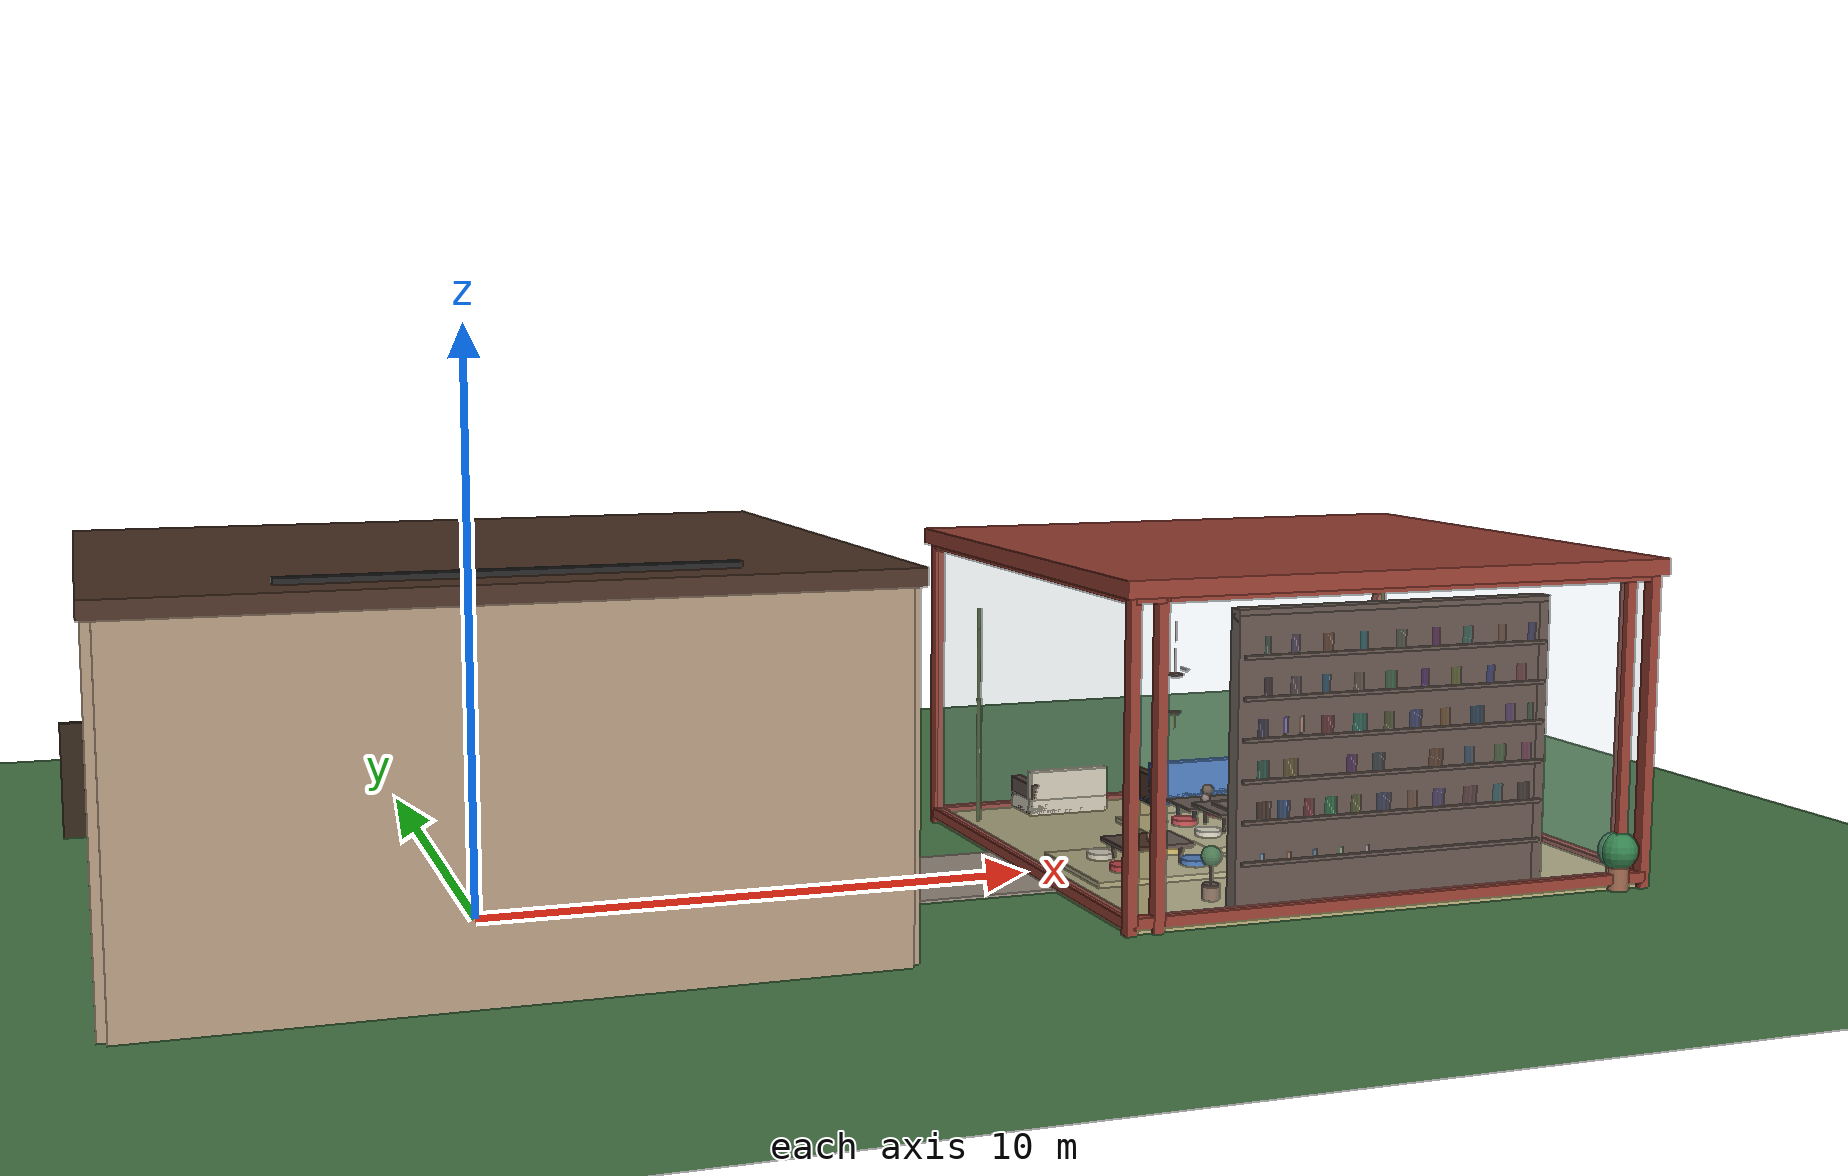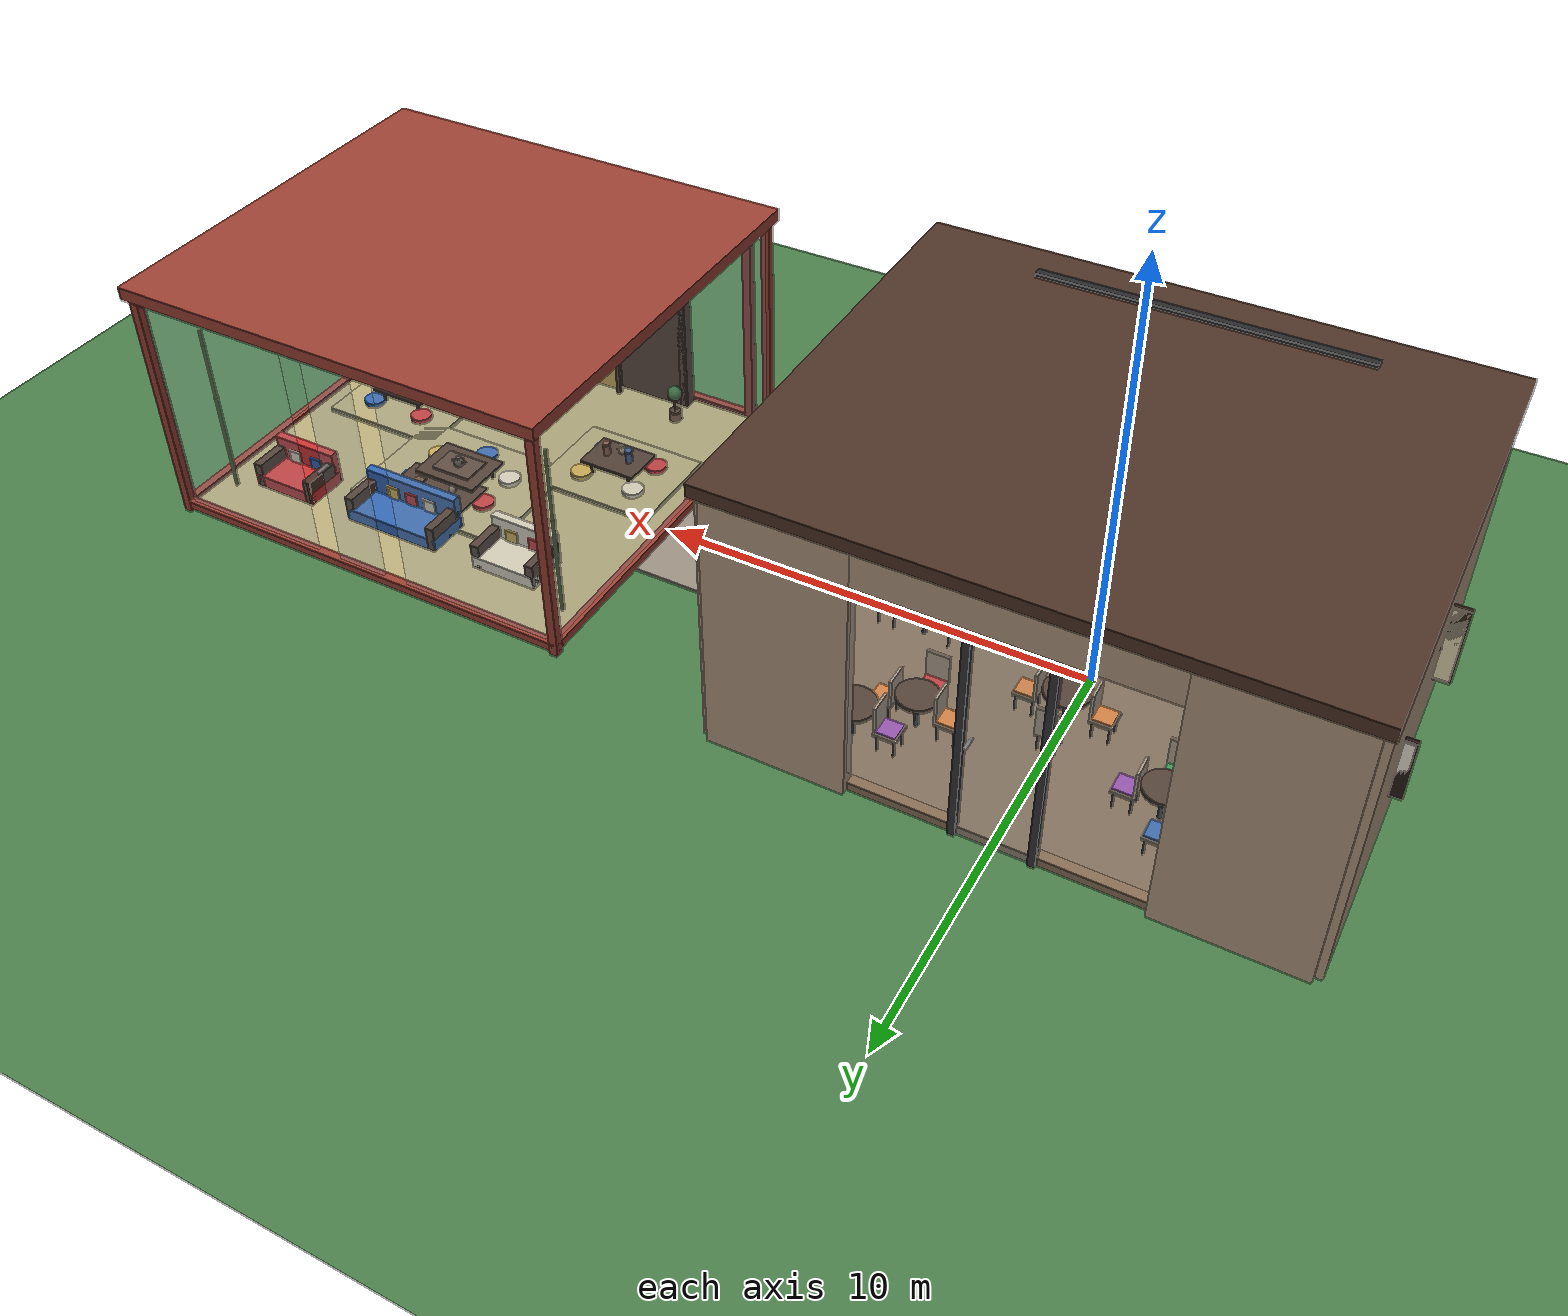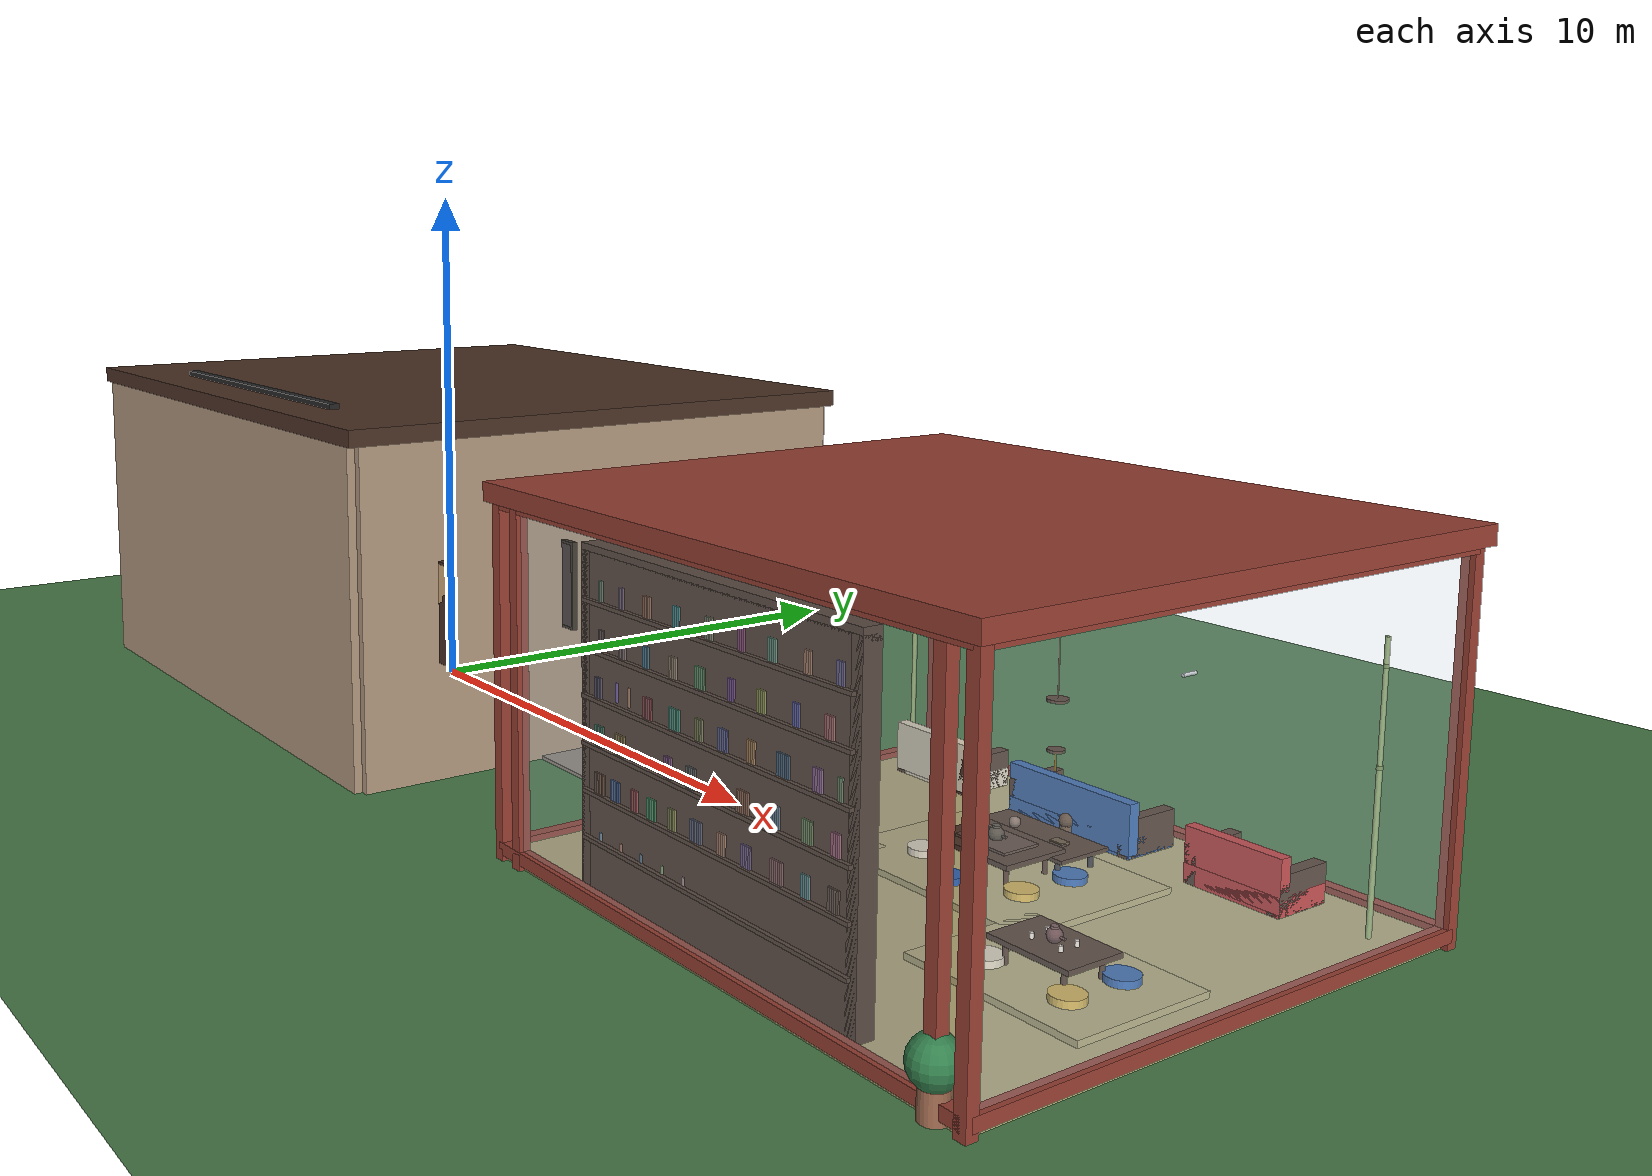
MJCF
<mujoco model="cafe_and_teahouse">
  <!-- 编译器设置 -->
  <compiler angle="degree" coordinate="local" inertiafromgeom="true"/>

  <!-- 物理选项 -->
  <option timestep="0.005" gravity="0 0 -9.81" iterations="50" solver="Newton" tolerance="1e-10">
    <flag contact="enable" gravity="enable"/>
  </option>

  <!-- 默认设置 -->
  <default>
    <geom conaffinity="1" condim="3" friction="1 0.5 0.005" solimp="0.9 0.95 0.001" solref="0.02 1"/>
    <joint damping="0.5" armature="0.01"/>
    <motor ctrlrange="-1 1" ctrllimited="true"/>
  </default>

  <!-- 视觉设置 -->
  <visual>
    <map force="0.1" zfar="100"/>
    <rgba haze="0.05 0.08 0.12 1"/>
    <quality shadowsize="4096"/>
    <global offwidth="1280" offheight="720"/>
  </visual>

  <!-- 资源定义 -->
  <asset>
    <!-- 木地板 -->
    <texture name="wood_floor" type="2d" builtin="checker" rgb1="0.55 0.45 0.35" rgb2="0.5 0.4 0.3" width="512" height="512"/>
    <material name="wood_floor_mat" texture="wood_floor" texrepeat="10 10" specular="0.3" shininess="0.3" reflectance="0.1"/>

    <!-- 榻榻米地板 -->
    <texture name="tatami" type="2d" builtin="checker" rgb1="0.75 0.7 0.5" rgb2="0.7 0.65 0.45" width="512" height="512"/>
    <material name="tatami_mat" texture="tatami" texrepeat="8 8" specular="0.1" shininess="0.1" reflectance="0"/>

    <!-- 高透明玻璃 -->
    <material name="glass_clear" rgba="0.8 0.9 0.95 0.15" specular="1" shininess="1" reflectance="0.7"/>

    <!-- 半透明玻璃门 -->
    <material name="glass_door" rgba="0.75 0.85 0.9 0.25" specular="1" shininess="1" reflectance="0.6"/>

    <!-- 金属材质 -->
    <material name="metal_dark" rgba="0.2 0.2 0.22 1" specular="0.9" shininess="0.8" reflectance="0.4"/>
    <material name="metal_chrome" rgba="0.8 0.8 0.82 1" specular="1" shininess="0.9" reflectance="0.6"/>

    <!-- 木材 -->
    <material name="wood_dark" rgba="0.3 0.2 0.15 1" specular="0.2" shininess="0.2" reflectance="0"/>
    <material name="wood_light" rgba="0.7 0.6 0.5 1" specular="0.3" shininess="0.3" reflectance="0.05"/>
    <material name="wood_red" rgba="0.6 0.25 0.2 1" specular="0.3" shininess="0.3" reflectance="0.05"/>
    <material name="bamboo" rgba="0.55 0.65 0.4 1" specular="0.2" shininess="0.2" reflectance="0.05"/>

    <!-- 布料 -->
    <material name="fabric_red" rgba="0.8 0.2 0.2 1" specular="0.1" shininess="0.1"/>
    <material name="fabric_blue" rgba="0.2 0.4 0.7 1" specular="0.1" shininess="0.1"/>
    <material name="fabric_green" rgba="0.2 0.6 0.3 1" specular="0.1" shininess="0.1"/>
    <material name="fabric_orange" rgba="0.9 0.5 0.2 1" specular="0.1" shininess="0.1"/>
    <material name="fabric_purple" rgba="0.6 0.3 0.7 1" specular="0.1" shininess="0.1"/>
    <material name="fabric_beige" rgba="0.9 0.85 0.75 1" specular="0.1" shininess="0.1"/>
    <material name="fabric_gold" rgba="0.85 0.7 0.3 1" specular="0.3" shininess="0.2"/>

    <!-- 纸质材料（屏风、灯笼） -->
    <material name="paper_white" rgba="0.95 0.93 0.88 0.8" specular="0.1" shininess="0.1"/>
    <material name="paper_red" rgba="0.9 0.2 0.15 0.7" specular="0.1" shininess="0.1"/>

    <!-- 草地 -->
    <texture name="grass" type="2d" builtin="checker" rgb1="0.3 0.5 0.3" rgb2="0.28 0.48 0.28" width="512" height="512"/>
    <material name="grass_mat" texture="grass" texrepeat="40 40" specular="0.1" shininess="0.05" reflectance="0"/>

    <!-- 天空 -->
    <texture name="skybox" type="skybox" builtin="gradient" rgb1="0.6 0.75 0.9" rgb2="0.3 0.5 0.7" width="512" height="512"/>
  </asset>

  <!-- 世界主体 -->
  <worldbody>
    <!-- 主光源（阳光 - 增强） -->
    <light directional="true" diffuse="1.2 1.2 1.1" specular="0.6 0.6 0.5" pos="30 20 40" dir="-1 -0.7 -1.5" castshadow="true"/>

    <!-- 辅助光源 - 增强 -->
    <light directional="true" diffuse="0.5 0.55 0.6" specular="0.3 0.3 0.3" pos="-20 -15 30" dir="0.7 0.5 -1" castshadow="false"/>

    <!-- 室内顶部光源 -->
    <light directional="false" diffuse="1.0 0.95 0.85" specular="0.4 0.4 0.3" pos="0 0 5.5" dir="0 0 -1" castshadow="false" cutoff="80"/>

    <!-- 地面 -->
    <geom name="ground" type="plane" size="50 50 0.1" material="grass_mat" condim="3" friction="1 0.5 0.005"/>

    <!-- ========== 咖啡店主体建筑 ========== -->
    <body name="cafe_building" pos="0 0 0">

      <!-- 地板 -->
      <geom name="cafe_floor" type="box" size="6 5 0.1" pos="0 0 0.1" material="wood_floor_mat"/>

      <!-- 后墙（实墙） -->
      <geom name="back_wall" type="box" size="6 0.15 3" pos="0 -5 3" material="wood_light"/>

      <!-- 左侧墙（实墙） -->
      <geom name="left_wall" type="box" size="0.15 5 3" pos="-6 0 3" material="wood_light"/>

      <!-- 右侧墙（实墙） -->
      <geom name="right_wall" type="box" size="0.15 5 3" pos="6 0 3" material="wood_light"/>

      <!-- 前墙左侧（实墙部分） -->
      <geom name="front_wall_left" type="box" size="1.5 0.15 3" pos="-4.5 5 3" material="wood_light"/>

      <!-- 前墙右侧（实墙部分） -->
      <geom name="front_wall_right" type="box" size="1.5 0.15 3" pos="4.5 5 3" material="wood_light"/>

      <!-- 前墙顶部横梁 -->
      <geom name="front_beam_top" type="box" size="3 0.15 0.4" pos="0 5 5.6" material="wood_light"/>

      <!-- 大型透明玻璃窗 - 前面 -->
      <geom name="front_glass_left" type="box" size="1.3 0.02 2.5" pos="-1.7 5 3" material="glass_clear"/>
      <geom name="front_glass_right" type="box" size="1.3 0.02 2.5" pos="1.7 5 3" material="glass_clear"/>

      <!-- 透明玻璃窗 - 左侧 -->
      <geom name="left_glass_1" type="box" size="0.02 2 2" pos="-6 -2 3" material="glass_clear"/>
      <geom name="left_glass_2" type="box" size="0.02 1.5 2" pos="-6 2 3" material="glass_clear"/>

      <!-- 透明玻璃窗 - 右侧 -->
      <geom name="right_glass_1" type="box" size="0.02 2 2" pos="6 -2 3" material="glass_clear"/>
      <geom name="right_glass_2" type="box" size="0.02 1.5 2" pos="6 2 3" material="glass_clear"/>

      <!-- 屋顶 -->
      <geom name="roof" type="box" size="6.2 5.2 0.15" pos="0 0 6.15" material="wood_dark"/>

      <!-- 门框 -->
      <geom name="door_frame_left" type="box" size="0.08 0.08 2.5" pos="-0.8 5 2.5" material="metal_dark"/>
      <geom name="door_frame_right" type="box" size="0.08 0.08 2.5" pos="0.8 5 2.5" material="metal_dark"/>
      <geom name="door_frame_top" type="box" size="0.8 0.08 0.08" pos="0 5 5" material="metal_dark"/>

    </body>

    <!-- ========== 动态玻璃门（可开合） ========== -->
    <body name="glass_door" pos="0 5 2.5">
      <joint name="door_hinge" type="hinge" pos="-0.7 0 0" axis="0 0 1" range="-5 90" damping="3" stiffness="5"/>
      <geom name="door_glass" type="box" size="0.7 0.03 2.5" pos="0 0 0" material="glass_door"/>
      <geom name="door_handle" type="cylinder" size="0.03 0.15" pos="0.6 0.08 0" quat="0.707 0.707 0 0" material="metal_chrome"/>
    </body>

    <!-- ========== 吧台区域（咖啡厅） ========== -->
    <body name="bar_counter" pos="0 -3.5 0">
      <!-- 吧台主体 -->
      <geom name="counter_top" type="box" size="4 0.8 0.05" pos="0 0 1.1" material="wood_dark"/>
      <geom name="counter_front" type="box" size="4 0.8 0.55" pos="0 0 0.55" material="wood_light"/>

      <!-- 吧台后墙架子（扩大） -->
      <geom name="back_shelf_back" type="box" size="4.5 0.15 3" pos="0 -0.7 3" material="wood_dark"/>
      <geom name="back_shelf_1" type="box" size="4.3 0.25 0.03" pos="0 -0.6 1.5" material="wood_dark"/>
      <geom name="back_shelf_2" type="box" size="4.3 0.25 0.03" pos="0 -0.6 2.1" material="wood_dark"/>
      <geom name="back_shelf_3" type="box" size="4.3 0.25 0.03" pos="0 -0.6 2.7" material="wood_dark"/>
      <geom name="back_shelf_4" type="box" size="4.3 0.25 0.03" pos="0 -0.6 3.3" material="wood_dark"/>
      <geom name="back_shelf_5" type="box" size="4.3 0.25 0.03" pos="0 -0.6 3.9" material="wood_dark"/>
      <geom name="back_shelf_6" type="box" size="4.3 0.25 0.03" pos="0 -0.6 4.5" material="wood_dark"/>

      <!-- ===== 咖啡机组（4台） ===== -->
      <!-- 咖啡机1（意式） -->
      <geom name="coffee_machine_1_base" type="box" size="0.5 0.35 0.3" pos="-3 -0.5 1.45" material="metal_dark"/>
      <geom name="coffee_machine_1_top" type="box" size="0.45 0.3 0.2" pos="-3 -0.5 1.85" material="metal_chrome"/>
      <geom name="coffee_machine_1_spout" type="cylinder" size="0.02 0.08" pos="-3 -0.4 1.7" material="metal_chrome"/>

      <!-- 咖啡机2（滴滤） -->
      <geom name="coffee_machine_2_base" type="box" size="0.35 0.3 0.25" pos="-1.8 -0.5 1.4" material="metal_dark"/>
      <geom name="coffee_machine_2_body" type="box" size="0.3 0.25 0.3" pos="-1.8 -0.5 1.8" rgba="0.2 0.2 0.2 1"/>
      <geom name="coffee_machine_2_pot" type="cylinder" size="0.08 0.12" pos="-1.8 -0.35 1.27" rgba="0.8 0.9 0.95 0.4"/>

      <!-- 咖啡机3（磨豆机） -->
      <geom name="grinder_base" type="cylinder" size="0.15 0.15" pos="-0.5 -0.5 1.3" material="metal_dark"/>
      <geom name="grinder_body" type="cylinder" size="0.12 0.2" pos="-0.5 -0.5 1.65" rgba="0.3 0.3 0.3 1"/>
      <geom name="grinder_hopper" type="cylinder" size="0.1 0.15" pos="-0.5 -0.5 2" rgba="0.8 0.9 0.95 0.3"/>

      <!-- 咖啡机4（手冲壶） -->
      <geom name="pour_over_stand" type="cylinder" size="0.02 0.25" pos="0.8 -0.5 1.4" material="metal_dark"/>
      <geom name="pour_over_filter" type="cylinder" size="0.08 0.08" pos="0.8 -0.5 1.6" rgba="0.9 0.9 0.85 0.7"/>
      <geom name="pour_over_pot" type="sphere" size="0.1" pos="0.8 -0.5 1.25" rgba="0.8 0.9 0.95 0.4"/>

      <!-- ===== 吧台上的咖啡杯（密密麻麻） ===== -->
      <!-- 第1排杯子 -->
      <geom name="counter_cup_1" type="cylinder" size="0.04 0.08" pos="-3.5 0.3 1.23" rgba="0.9 0.85 0.75 1"/>
      <geom name="counter_cup_2" type="cylinder" size="0.04 0.08" pos="-3.2 0.3 1.23" rgba="0.85 0.8 0.7 1"/>
      <geom name="counter_cup_3" type="cylinder" size="0.04 0.08" pos="-2.9 0.3 1.23" rgba="0.9 0.85 0.75 1"/>
      <geom name="counter_cup_4" type="cylinder" size="0.04 0.08" pos="-2.6 0.3 1.23" rgba="0.85 0.8 0.7 1"/>
      <geom name="counter_cup_5" type="cylinder" size="0.04 0.08" pos="-2.3 0.3 1.23" rgba="0.9 0.85 0.75 1"/>
      <geom name="counter_cup_6" type="cylinder" size="0.04 0.08" pos="-2 0.3 1.23" rgba="0.85 0.8 0.7 1"/>
      <geom name="counter_cup_7" type="cylinder" size="0.04 0.08" pos="-1.7 0.3 1.23" rgba="0.9 0.85 0.75 1"/>
      <geom name="counter_cup_8" type="cylinder" size="0.04 0.08" pos="-1.4 0.3 1.23" rgba="0.85 0.8 0.7 1"/>
      <geom name="counter_cup_9" type="cylinder" size="0.04 0.08" pos="-1.1 0.3 1.23" rgba="0.9 0.85 0.75 1"/>
      <geom name="counter_cup_10" type="cylinder" size="0.04 0.08" pos="-0.8 0.3 1.23" rgba="0.85 0.8 0.7 1"/>
      <geom name="counter_cup_11" type="cylinder" size="0.04 0.08" pos="-0.5 0.3 1.23" rgba="0.9 0.85 0.75 1"/>
      <geom name="counter_cup_12" type="cylinder" size="0.04 0.08" pos="-0.2 0.3 1.23" rgba="0.85 0.8 0.7 1"/>
      <geom name="counter_cup_13" type="cylinder" size="0.04 0.08" pos="0.1 0.3 1.23" rgba="0.9 0.85 0.75 1"/>
      <geom name="counter_cup_14" type="cylinder" size="0.04 0.08" pos="0.4 0.3 1.23" rgba="0.85 0.8 0.7 1"/>
      <geom name="counter_cup_15" type="cylinder" size="0.04 0.08" pos="0.7 0.3 1.23" rgba="0.9 0.85 0.75 1"/>
      <geom name="counter_cup_16" type="cylinder" size="0.04 0.08" pos="1 0.3 1.23" rgba="0.85 0.8 0.7 1"/>
      <geom name="counter_cup_17" type="cylinder" size="0.04 0.08" pos="1.3 0.3 1.23" rgba="0.9 0.85 0.75 1"/>
      <geom name="counter_cup_18" type="cylinder" size="0.04 0.08" pos="1.6 0.3 1.23" rgba="0.85 0.8 0.7 1"/>
      <geom name="counter_cup_19" type="cylinder" size="0.04 0.08" pos="1.9 0.3 1.23" rgba="0.9 0.85 0.75 1"/>
      <geom name="counter_cup_20" type="cylinder" size="0.04 0.08" pos="2.2 0.3 1.23" rgba="0.85 0.8 0.7 1"/>

      <!-- 第2排杯子（小杯） -->
      <geom name="counter_cup_21" type="cylinder" size="0.03 0.06" pos="-3.5 0.5 1.21" rgba="0.9 0.9 0.9 1"/>
      <geom name="counter_cup_22" type="cylinder" size="0.03 0.06" pos="-3.3 0.5 1.21" rgba="0.85 0.85 0.85 1"/>
      <geom name="counter_cup_23" type="cylinder" size="0.03 0.06" pos="-3.1 0.5 1.21" rgba="0.9 0.9 0.9 1"/>
      <geom name="counter_cup_24" type="cylinder" size="0.03 0.06" pos="-2.9 0.5 1.21" rgba="0.85 0.85 0.85 1"/>
      <geom name="counter_cup_25" type="cylinder" size="0.03 0.06" pos="-2.7 0.5 1.21" rgba="0.9 0.9 0.9 1"/>
      <geom name="counter_cup_26" type="cylinder" size="0.03 0.06" pos="-2.5 0.5 1.21" rgba="0.85 0.85 0.85 1"/>
      <geom name="counter_cup_27" type="cylinder" size="0.03 0.06" pos="-2.3 0.5 1.21" rgba="0.9 0.9 0.9 1"/>
      <geom name="counter_cup_28" type="cylinder" size="0.03 0.06" pos="-2.1 0.5 1.21" rgba="0.85 0.85 0.85 1"/>
      <geom name="counter_cup_29" type="cylinder" size="0.03 0.06" pos="-1.9 0.5 1.21" rgba="0.9 0.9 0.9 1"/>
      <geom name="counter_cup_30" type="cylinder" size="0.03 0.06" pos="-1.7 0.5 1.21" rgba="0.85 0.85 0.85 1"/>

      <!-- ===== 架子上的瓶瓶罐罐（密密麻麻，各色液体） ===== -->
      <!-- 第1层 - 咖啡糖浆瓶 -->
      <geom name="syrup_1_bottle" type="cylinder" size="0.04 0.15" pos="-4 -0.58 1.65" rgba="0.8 0.9 0.95 0.3"/>
      <geom name="syrup_1_liquid" type="cylinder" size="0.035 0.12" pos="-4 -0.58 1.62" rgba="0.8 0.6 0.3 0.7"/>

      <geom name="syrup_2_bottle" type="cylinder" size="0.04 0.15" pos="-3.7 -0.58 1.65" rgba="0.8 0.9 0.95 0.3"/>
      <geom name="syrup_2_liquid" type="cylinder" size="0.035 0.12" pos="-3.7 -0.58 1.62" rgba="0.6 0.3 0.2 0.7"/>

      <geom name="syrup_3_bottle" type="cylinder" size="0.04 0.15" pos="-3.4 -0.58 1.65" rgba="0.8 0.9 0.95 0.3"/>
      <geom name="syrup_3_liquid" type="cylinder" size="0.035 0.12" pos="-3.4 -0.58 1.62" rgba="0.9 0.5 0.2 0.7"/>

      <geom name="syrup_4_bottle" type="cylinder" size="0.04 0.15" pos="-3.1 -0.58 1.65" rgba="0.8 0.9 0.95 0.3"/>
      <geom name="syrup_4_liquid" type="cylinder" size="0.035 0.12" pos="-3.1 -0.58 1.62" rgba="0.4 0.7 0.3 0.7"/>

      <geom name="syrup_5_bottle" type="cylinder" size="0.04 0.15" pos="-2.8 -0.58 1.65" rgba="0.8 0.9 0.95 0.3"/>
      <geom name="syrup_5_liquid" type="cylinder" size="0.035 0.12" pos="-2.8 -0.58 1.62" rgba="0.9 0.2 0.2 0.7"/>

      <geom name="syrup_6_bottle" type="cylinder" size="0.04 0.15" pos="-2.5 -0.58 1.65" rgba="0.8 0.9 0.95 0.3"/>
      <geom name="syrup_6_liquid" type="cylinder" size="0.035 0.12" pos="-2.5 -0.58 1.62" rgba="0.3 0.5 0.8 0.7"/>

      <geom name="syrup_7_bottle" type="cylinder" size="0.04 0.15" pos="-2.2 -0.58 1.65" rgba="0.8 0.9 0.95 0.3"/>
      <geom name="syrup_7_liquid" type="cylinder" size="0.035 0.12" pos="-2.2 -0.58 1.62" rgba="0.9 0.7 0.4 0.7"/>

      <geom name="syrup_8_bottle" type="cylinder" size="0.04 0.15" pos="-1.9 -0.58 1.65" rgba="0.8 0.9 0.95 0.3"/>
      <geom name="syrup_8_liquid" type="cylinder" size="0.035 0.12" pos="-1.9 -0.58 1.62" rgba="0.95 0.85 0.3 0.7"/>

      <geom name="syrup_9_bottle" type="cylinder" size="0.04 0.15" pos="-1.6 -0.58 1.65" rgba="0.8 0.9 0.95 0.3"/>
      <geom name="syrup_9_liquid" type="cylinder" size="0.035 0.12" pos="-1.6 -0.58 1.62" rgba="0.5 0.3 0.6 0.7"/>

      <geom name="syrup_10_bottle" type="cylinder" size="0.04 0.15" pos="-1.3 -0.58 1.65" rgba="0.8 0.9 0.95 0.3"/>
      <geom name="syrup_10_liquid" type="cylinder" size="0.035 0.12" pos="-1.3 -0.58 1.62" rgba="0.3 0.8 0.5 0.7"/>

      <geom name="syrup_11_bottle" type="cylinder" size="0.04 0.15" pos="-1 -0.58 1.65" rgba="0.8 0.9 0.95 0.3"/>
      <geom name="syrup_11_liquid" type="cylinder" size="0.035 0.12" pos="-1 -0.58 1.62" rgba="0.7 0.4 0.3 0.7"/>

      <geom name="syrup_12_bottle" type="cylinder" size="0.04 0.15" pos="-0.7 -0.58 1.65" rgba="0.8 0.9 0.95 0.3"/>
      <geom name="syrup_12_liquid" type="cylinder" size="0.035 0.12" pos="-0.7 -0.58 1.62" rgba="0.9 0.3 0.5 0.7"/>

      <geom name="syrup_13_bottle" type="cylinder" size="0.04 0.15" pos="-0.4 -0.58 1.65" rgba="0.8 0.9 0.95 0.3"/>
      <geom name="syrup_13_liquid" type="cylinder" size="0.035 0.12" pos="-0.4 -0.58 1.62" rgba="0.4 0.6 0.8 0.7"/>

      <geom name="syrup_14_bottle" type="cylinder" size="0.04 0.15" pos="-0.1 -0.58 1.65" rgba="0.8 0.9 0.95 0.3"/>
      <geom name="syrup_14_liquid" type="cylinder" size="0.035 0.12" pos="-0.1 -0.58 1.62" rgba="0.8 0.5 0.2 0.7"/>

      <geom name="syrup_15_bottle" type="cylinder" size="0.04 0.15" pos="0.2 -0.58 1.65" rgba="0.8 0.9 0.95 0.3"/>
      <geom name="syrup_15_liquid" type="cylinder" size="0.035 0.12" pos="0.2 -0.58 1.62" rgba="0.6 0.7 0.3 0.7"/>

      <geom name="syrup_16_bottle" type="cylinder" size="0.04 0.15" pos="0.5 -0.58 1.65" rgba="0.8 0.9 0.95 0.3"/>
      <geom name="syrup_16_liquid" type="cylinder" size="0.035 0.12" pos="0.5 -0.58 1.62" rgba="0.9 0.6 0.4 0.7"/>

      <geom name="syrup_17_bottle" type="cylinder" size="0.04 0.15" pos="0.8 -0.58 1.65" rgba="0.8 0.9 0.95 0.3"/>
      <geom name="syrup_17_liquid" type="cylinder" size="0.035 0.12" pos="0.8 -0.58 1.62" rgba="0.3 0.4 0.7 0.7"/>

      <geom name="syrup_18_bottle" type="cylinder" size="0.04 0.15" pos="1.1 -0.58 1.65" rgba="0.8 0.9 0.95 0.3"/>
      <geom name="syrup_18_liquid" type="cylinder" size="0.035 0.12" pos="1.1 -0.58 1.62" rgba="0.7 0.3 0.4 0.7"/>

      <geom name="syrup_19_bottle" type="cylinder" size="0.04 0.15" pos="1.4 -0.58 1.65" rgba="0.8 0.9 0.95 0.3"/>
      <geom name="syrup_19_liquid" type="cylinder" size="0.035 0.12" pos="1.4 -0.58 1.62" rgba="0.5 0.8 0.4 0.7"/>

      <geom name="syrup_20_bottle" type="cylinder" size="0.04 0.15" pos="1.7 -0.58 1.65" rgba="0.8 0.9 0.95 0.3"/>
      <geom name="syrup_20_liquid" type="cylinder" size="0.035 0.12" pos="1.7 -0.58 1.62" rgba="0.9 0.4 0.3 0.7"/>

      <geom name="syrup_21_bottle" type="cylinder" size="0.04 0.15" pos="2 -0.58 1.65" rgba="0.8 0.9 0.95 0.3"/>
      <geom name="syrup_21_liquid" type="cylinder" size="0.035 0.12" pos="2 -0.58 1.62" rgba="0.4 0.3 0.6 0.7"/>

      <geom name="syrup_22_bottle" type="cylinder" size="0.04 0.15" pos="2.3 -0.58 1.65" rgba="0.8 0.9 0.95 0.3"/>
      <geom name="syrup_22_liquid" type="cylinder" size="0.035 0.12" pos="2.3 -0.58 1.62" rgba="0.8 0.6 0.5 0.7"/>

      <geom name="syrup_23_bottle" type="cylinder" size="0.04 0.15" pos="2.6 -0.58 1.65" rgba="0.8 0.9 0.95 0.3"/>
      <geom name="syrup_23_liquid" type="cylinder" size="0.035 0.12" pos="2.6 -0.58 1.62" rgba="0.3 0.6 0.7 0.7"/>

      <geom name="syrup_24_bottle" type="cylinder" size="0.04 0.15" pos="2.9 -0.58 1.65" rgba="0.8 0.9 0.95 0.3"/>
      <geom name="syrup_24_liquid" type="cylinder" size="0.035 0.12" pos="2.9 -0.58 1.62" rgba="0.9 0.5 0.6 0.7"/>

      <geom name="syrup_25_bottle" type="cylinder" size="0.04 0.15" pos="3.2 -0.58 1.65" rgba="0.8 0.9 0.95 0.3"/>
      <geom name="syrup_25_liquid" type="cylinder" size="0.035 0.12" pos="3.2 -0.58 1.62" rgba="0.6 0.4 0.3 0.7"/>

      <geom name="syrup_26_bottle" type="cylinder" size="0.04 0.15" pos="3.5 -0.58 1.65" rgba="0.8 0.9 0.95 0.3"/>
      <geom name="syrup_26_liquid" type="cylinder" size="0.035 0.12" pos="3.5 -0.58 1.62" rgba="0.7 0.7 0.3 0.7"/>

      <geom name="syrup_27_bottle" type="cylinder" size="0.04 0.15" pos="3.8 -0.58 1.65" rgba="0.8 0.9 0.95 0.3"/>
      <geom name="syrup_27_liquid" type="cylinder" size="0.035 0.12" pos="3.8 -0.58 1.62" rgba="0.5 0.5 0.8 0.7"/>

      <!-- 第2层 - 各色饮料瓶 -->
      <geom name="drink_1_bottle" type="cylinder" size="0.045 0.14" pos="-4 -0.58 2.24" rgba="0.75 0.85 0.9 0.25"/>
      <geom name="drink_1_liquid" type="cylinder" size="0.038 0.11" pos="-4 -0.58 2.21" rgba="0.9 0.7 0.2 0.65"/>

      <geom name="drink_2_bottle" type="cylinder" size="0.045 0.14" pos="-3.7 -0.58 2.24" rgba="0.2 0.3 0.2 0.5"/>
      <geom name="drink_2_liquid" type="cylinder" size="0.038 0.11" pos="-3.7 -0.58 2.21" rgba="0.6 0.1 0.15 0.7"/>

      <geom name="drink_3_bottle" type="cylinder" size="0.045 0.14" pos="-3.4 -0.58 2.24" rgba="0.75 0.85 0.9 0.25"/>
      <geom name="drink_3_liquid" type="cylinder" size="0.038 0.11" pos="-3.4 -0.58 2.21" rgba="0.3 0.7 0.4 0.65"/>

      <geom name="drink_4_bottle" type="cylinder" size="0.045 0.14" pos="-3.1 -0.58 2.24" rgba="0.75 0.85 0.9 0.25"/>
      <geom name="drink_4_liquid" type="cylinder" size="0.038 0.11" pos="-3.1 -0.58 2.21" rgba="0.8 0.4 0.2 0.65"/>

      <geom name="drink_5_bottle" type="cylinder" size="0.045 0.14" pos="-2.8 -0.58 2.24" rgba="0.75 0.85 0.9 0.25"/>
      <geom name="drink_5_liquid" type="cylinder" size="0.038 0.11" pos="-2.8 -0.58 2.21" rgba="0.95 0.95 0.9 0.8"/>

      <geom name="drink_6_bottle" type="cylinder" size="0.045 0.14" pos="-2.5 -0.58 2.24" rgba="0.75 0.85 0.9 0.25"/>
      <geom name="drink_6_liquid" type="cylinder" size="0.038 0.11" pos="-2.5 -0.58 2.21" rgba="0.4 0.6 0.3 0.6"/>

      <geom name="drink_7_bottle" type="cylinder" size="0.045 0.14" pos="-2.2 -0.58 2.24" rgba="0.3 0.2 0.1 0.4"/>
      <geom name="drink_7_liquid" type="cylinder" size="0.038 0.11" pos="-2.2 -0.58 2.21" rgba="0.8 0.6 0.2 0.6"/>

      <geom name="drink_8_bottle" type="cylinder" size="0.045 0.14" pos="-1.9 -0.58 2.24" rgba="0.75 0.85 0.9 0.25"/>
      <geom name="drink_8_liquid" type="cylinder" size="0.038 0.11" pos="-1.9 -0.58 2.21" rgba="0.9 0.3 0.4 0.7"/>

      <geom name="drink_9_bottle" type="cylinder" size="0.045 0.14" pos="-1.6 -0.58 2.24" rgba="0.75 0.85 0.9 0.25"/>
      <geom name="drink_9_liquid" type="cylinder" size="0.038 0.11" pos="-1.6 -0.58 2.21" rgba="0.3 0.8 0.4 0.6"/>

      <geom name="drink_10_bottle" type="cylinder" size="0.045 0.14" pos="-1.3 -0.58 2.24" rgba="0.9 0.95 1 0.2"/>
      <geom name="drink_10_liquid" type="cylinder" size="0.038 0.11" pos="-1.3 -0.58 2.21" rgba="0.95 0.95 0.98 0.5"/>

      <geom name="drink_11_bottle" type="cylinder" size="0.045 0.14" pos="-1 -0.58 2.24" rgba="0.2 0.3 0.2 0.5"/>
      <geom name="drink_11_liquid" type="cylinder" size="0.038 0.11" pos="-1 -0.58 2.21" rgba="0.5 0.2 0.3 0.75"/>

      <geom name="drink_12_bottle" type="cylinder" size="0.045 0.14" pos="-0.7 -0.58 2.24" rgba="0.75 0.85 0.9 0.25"/>
      <geom name="drink_12_liquid" type="cylinder" size="0.038 0.11" pos="-0.7 -0.58 2.21" rgba="0.95 0.9 0.3 0.65"/>

      <geom name="drink_13_bottle" type="cylinder" size="0.045 0.14" pos="-0.4 -0.58 2.24" rgba="0.2 0.3 0.2 0.5"/>
      <geom name="drink_13_liquid" type="cylinder" size="0.038 0.11" pos="-0.4 -0.58 2.21" rgba="0.9 0.85 0.5 0.6"/>

      <geom name="drink_14_bottle" type="cylinder" size="0.045 0.14" pos="-0.1 -0.58 2.24" rgba="0.75 0.85 0.9 0.25"/>
      <geom name="drink_14_liquid" type="cylinder" size="0.038 0.11" pos="-0.1 -0.58 2.21" rgba="0.85 0.92 0.98 0.5"/>

      <geom name="drink_15_bottle" type="cylinder" size="0.045 0.14" pos="0.2 -0.58 2.24" rgba="0.4 0.3 0.2 0.4"/>
      <geom name="drink_15_liquid" type="cylinder" size="0.038 0.11" pos="0.2 -0.58 2.21" rgba="0.7 0.5 0.2 0.7"/>

      <geom name="drink_16_bottle" type="cylinder" size="0.045 0.14" pos="0.5 -0.58 2.24" rgba="0.75 0.85 0.9 0.25"/>
      <geom name="drink_16_liquid" type="cylinder" size="0.038 0.11" pos="0.5 -0.58 2.21" rgba="0.9 0.95 1 0.3"/>

      <geom name="drink_17_bottle" type="cylinder" size="0.045 0.14" pos="0.8 -0.58 2.24" rgba="0.75 0.85 0.9 0.25"/>
      <geom name="drink_17_liquid" type="cylinder" size="0.038 0.11" pos="0.8 -0.58 2.21" rgba="0.2 0.4 0.9 0.7"/>

      <geom name="drink_18_bottle" type="cylinder" size="0.045 0.14" pos="1.1 -0.58 2.24" rgba="0.75 0.85 0.9 0.25"/>
      <geom name="drink_18_liquid" type="cylinder" size="0.038 0.11" pos="1.1 -0.58 2.21" rgba="0.8 0.7 0.6 0.75"/>

      <geom name="drink_19_bottle" type="cylinder" size="0.045 0.14" pos="1.4 -0.58 2.24" rgba="0.75 0.85 0.9 0.25"/>
      <geom name="drink_19_liquid" type="cylinder" size="0.038 0.11" pos="1.4 -0.58 2.21" rgba="0.3 0.2 0.6 0.7"/>

      <geom name="drink_20_bottle" type="cylinder" size="0.045 0.14" pos="1.7 -0.58 2.24" rgba="0.75 0.85 0.9 0.25"/>
      <geom name="drink_20_liquid" type="cylinder" size="0.038 0.11" pos="1.7 -0.58 2.21" rgba="0.6 0.4 0.2 0.6"/>

      <!-- 第3层 - 继续密密麻麻的瓶子 -->
      <geom name="bottle_3_1" type="cylinder" size="0.04 0.13" pos="-3.8 -0.58 2.83" rgba="0.75 0.85 0.9 0.25"/>
      <geom name="bottle_3_1_liq" type="cylinder" size="0.035 0.1" pos="-3.8 -0.58 2.8" rgba="0.9 0.5 0.3 0.65"/>

      <geom name="bottle_3_2" type="cylinder" size="0.04 0.13" pos="-3.5 -0.58 2.83" rgba="0.75 0.85 0.9 0.25"/>
      <geom name="bottle_3_2_liq" type="cylinder" size="0.035 0.1" pos="-3.5 -0.58 2.8" rgba="0.4 0.7 0.5 0.65"/>

      <geom name="bottle_3_3" type="cylinder" size="0.04 0.13" pos="-3.2 -0.58 2.83" rgba="0.75 0.85 0.9 0.25"/>
      <geom name="bottle_3_3_liq" type="cylinder" size="0.035 0.1" pos="-3.2 -0.58 2.8" rgba="0.8 0.3 0.4 0.65"/>

      <geom name="bottle_3_4" type="cylinder" size="0.04 0.13" pos="-2.9 -0.58 2.83" rgba="0.75 0.85 0.9 0.25"/>
      <geom name="bottle_3_4_liq" type="cylinder" size="0.035 0.1" pos="-2.9 -0.58 2.8" rgba="0.3 0.5 0.8 0.65"/>

      <geom name="bottle_3_5" type="cylinder" size="0.04 0.13" pos="-2.6 -0.58 2.83" rgba="0.75 0.85 0.9 0.25"/>
      <geom name="bottle_3_5_liq" type="cylinder" size="0.035 0.1" pos="-2.6 -0.58 2.8" rgba="0.9 0.7 0.2 0.65"/>

      <geom name="bottle_3_6" type="cylinder" size="0.04 0.13" pos="-2.3 -0.58 2.83" rgba="0.75 0.85 0.9 0.25"/>
      <geom name="bottle_3_6_liq" type="cylinder" size="0.035 0.1" pos="-2.3 -0.58 2.8" rgba="0.6 0.3 0.6 0.65"/>

      <geom name="bottle_3_7" type="cylinder" size="0.04 0.13" pos="-2 -0.58 2.83" rgba="0.75 0.85 0.9 0.25"/>
      <geom name="bottle_3_7_liq" type="cylinder" size="0.035 0.1" pos="-2 -0.58 2.8" rgba="0.5 0.8 0.4 0.65"/>

      <geom name="bottle_3_8" type="cylinder" size="0.04 0.13" pos="-1.7 -0.58 2.83" rgba="0.75 0.85 0.9 0.25"/>
      <geom name="bottle_3_8_liq" type="cylinder" size="0.035 0.1" pos="-1.7 -0.58 2.8" rgba="0.9 0.4 0.3 0.65"/>

      <geom name="bottle_3_9" type="cylinder" size="0.04 0.13" pos="-1.4 -0.58 2.83" rgba="0.75 0.85 0.9 0.25"/>
      <geom name="bottle_3_9_liq" type="cylinder" size="0.035 0.1" pos="-1.4 -0.58 2.8" rgba="0.7 0.6 0.3 0.65"/>

      <geom name="bottle_3_10" type="cylinder" size="0.04 0.13" pos="-1.1 -0.58 2.83" rgba="0.75 0.85 0.9 0.25"/>
      <geom name="bottle_3_10_liq" type="cylinder" size="0.035 0.1" pos="-1.1 -0.58 2.8" rgba="0.4 0.4 0.7 0.65"/>

      <geom name="bottle_3_11" type="cylinder" size="0.04 0.13" pos="-0.8 -0.58 2.83" rgba="0.75 0.85 0.9 0.25"/>
      <geom name="bottle_3_11_liq" type="cylinder" size="0.035 0.1" pos="-0.8 -0.58 2.8" rgba="0.8 0.5 0.5 0.65"/>

      <geom name="bottle_3_12" type="cylinder" size="0.04 0.13" pos="-0.5 -0.58 2.83" rgba="0.75 0.85 0.9 0.25"/>
      <geom name="bottle_3_12_liq" type="cylinder" size="0.035 0.1" pos="-0.5 -0.58 2.8" rgba="0.3 0.7 0.6 0.65"/>

      <geom name="bottle_3_13" type="cylinder" size="0.04 0.13" pos="-0.2 -0.58 2.83" rgba="0.75 0.85 0.9 0.25"/>
      <geom name="bottle_3_13_liq" type="cylinder" size="0.035 0.1" pos="-0.2 -0.58 2.8" rgba="0.9 0.6 0.4 0.65"/>

      <geom name="bottle_3_14" type="cylinder" size="0.04 0.13" pos="0.1 -0.58 2.83" rgba="0.75 0.85 0.9 0.25"/>
      <geom name="bottle_3_14_liq" type="cylinder" size="0.035 0.1" pos="0.1 -0.58 2.8" rgba="0.5 0.5 0.8 0.65"/>

      <geom name="bottle_3_15" type="cylinder" size="0.04 0.13" pos="0.4 -0.58 2.83" rgba="0.75 0.85 0.9 0.25"/>
      <geom name="bottle_3_15_liq" type="cylinder" size="0.035 0.1" pos="0.4 -0.58 2.8" rgba="0.8 0.7 0.3 0.65"/>

      <geom name="bottle_3_16" type="cylinder" size="0.04 0.13" pos="0.7 -0.58 2.83" rgba="0.75 0.85 0.9 0.25"/>
      <geom name="bottle_3_16_liq" type="cylinder" size="0.035 0.1" pos="0.7 -0.58 2.8" rgba="0.6 0.3 0.5 0.65"/>

      <geom name="bottle_3_17" type="cylinder" size="0.04 0.13" pos="1 -0.58 2.83" rgba="0.75 0.85 0.9 0.25"/>
      <geom name="bottle_3_17_liq" type="cylinder" size="0.035 0.1" pos="1 -0.58 2.8" rgba="0.4 0.6 0.7 0.65"/>

      <geom name="bottle_3_18" type="cylinder" size="0.04 0.13" pos="1.3 -0.58 2.83" rgba="0.75 0.85 0.9 0.25"/>
      <geom name="bottle_3_18_liq" type="cylinder" size="0.035 0.1" pos="1.3 -0.58 2.8" rgba="0.9 0.5 0.5 0.65"/>

      <!-- 第4-6层继续放瓶子 -->
      <geom name="bottle_4_1" type="cylinder" size="0.04 0.12" pos="-3.6 -0.58 3.42" rgba="0.75 0.85 0.9 0.25"/>
      <geom name="bottle_4_1_liq" type="cylinder" size="0.035 0.09" pos="-3.6 -0.58 3.39" rgba="0.7 0.5 0.3 0.65"/>

      <geom name="bottle_4_2" type="cylinder" size="0.04 0.12" pos="-3.3 -0.58 3.42" rgba="0.75 0.85 0.9 0.25"/>
      <geom name="bottle_4_2_liq" type="cylinder" size="0.035 0.09" pos="-3.3 -0.58 3.39" rgba="0.5 0.7 0.4 0.65"/>

      <geom name="bottle_4_3" type="cylinder" size="0.04 0.12" pos="-3 -0.58 3.42" rgba="0.75 0.85 0.9 0.25"/>
      <geom name="bottle_4_3_liq" type="cylinder" size="0.035 0.09" pos="-3 -0.58 3.39" rgba="0.8 0.4 0.3 0.65"/>

      <geom name="bottle_4_4" type="cylinder" size="0.04 0.12" pos="-2.7 -0.58 3.42" rgba="0.75 0.85 0.9 0.25"/>
      <geom name="bottle_4_4_liq" type="cylinder" size="0.035 0.09" pos="-2.7 -0.58 3.39" rgba="0.4 0.5 0.8 0.65"/>

      <geom name="bottle_4_5" type="cylinder" size="0.04 0.12" pos="-2.4 -0.58 3.42" rgba="0.75 0.85 0.9 0.25"/>
      <geom name="bottle_4_5_liq" type="cylinder" size="0.035 0.09" pos="-2.4 -0.58 3.39" rgba="0.9 0.6 0.3 0.65"/>

      <geom name="bottle_5_1" type="cylinder" size="0.04 0.12" pos="-3.4 -0.58 4.02" rgba="0.75 0.85 0.9 0.25"/>
      <geom name="bottle_5_1_liq" type="cylinder" size="0.035 0.09" pos="-3.4 -0.58 3.99" rgba="0.6 0.4 0.5 0.65"/>

      <geom name="bottle_5_2" type="cylinder" size="0.04 0.12" pos="-3.1 -0.58 4.02" rgba="0.75 0.85 0.9 0.25"/>
      <geom name="bottle_5_2_liq" type="cylinder" size="0.035 0.09" pos="-3.1 -0.58 3.99" rgba="0.5 0.6 0.7 0.65"/>

      <geom name="bottle_5_3" type="cylinder" size="0.04 0.12" pos="-2.8 -0.58 4.02" rgba="0.75 0.85 0.9 0.25"/>
      <geom name="bottle_5_3_liq" type="cylinder" size="0.035 0.09" pos="-2.8 -0.58 3.99" rgba="0.8 0.5 0.4 0.65"/>

      <geom name="bottle_6_1" type="cylinder" size="0.04 0.11" pos="-3.2 -0.58 4.61" rgba="0.75 0.85 0.9 0.25"/>
      <geom name="bottle_6_1_liq" type="cylinder" size="0.035 0.08" pos="-3.2 -0.58 4.58" rgba="0.7 0.6 0.4 0.65"/>

      <geom name="bottle_6_2" type="cylinder" size="0.04 0.11" pos="-2.9 -0.58 4.61" rgba="0.75 0.85 0.9 0.25"/>
      <geom name="bottle_6_2_liq" type="cylinder" size="0.035 0.08" pos="-2.9 -0.58 4.58" rgba="0.5 0.7 0.5 0.65"/>

      <!-- ===== 吧台菜单 ===== -->
      <!-- 立式菜单板1 -->
      <geom name="menu_board_1_stand" type="cylinder" size="0.02 0.25" pos="-3.5 0.65 1.4" material="metal_dark"/>
      <geom name="menu_board_1" type="box" size="0.15 0.01 0.25" pos="-3.5 0.65 1.55" rgba="0.2 0.2 0.2 1"/>
      <geom name="menu_text_1" type="box" size="0.12 0.005 0.2" pos="-3.5 0.66 1.55" rgba="0.95 0.95 0.9 1"/>

      <!-- 立式菜单板2 -->
      <geom name="menu_board_2_stand" type="cylinder" size="0.02 0.25" pos="3.5 0.65 1.4" material="metal_dark"/>
      <geom name="menu_board_2" type="box" size="0.15 0.01 0.25" pos="3.5 0.65 1.55" rgba="0.2 0.2 0.2 1"/>
      <geom name="menu_text_2" type="box" size="0.12 0.005 0.2" pos="3.5 0.66 1.55" rgba="0.95 0.95 0.9 1"/>

      <!-- 平放菜单卡片 -->
      <geom name="menu_card_1" type="box" size="0.12 0.08 0.002" pos="2.8 0.5 1.152" rgba="0.95 0.95 0.9 1"/>
      <geom name="menu_card_2" type="box" size="0.12 0.08 0.002" pos="1.5 0.5 1.152" rgba="0.95 0.95 0.9 1"/>
      <geom name="menu_card_3" type="box" size="0.12 0.08 0.002" pos="0.2 0.5 1.152" rgba="0.95 0.95 0.9 1"/>
      <geom name="menu_card_4" type="box" size="0.12 0.08 0.002" pos="-1 0.5 1.152" rgba="0.95 0.95 0.9 1"/>

      <!-- 吧台内部灯光 -->
      <light mode="fixed" directional="false" diffuse="1 0.9 0.7" specular="0.5 0.4 0.3" pos="0 -0.3 3" dir="0 0 -1" castshadow="false" cutoff="45"/>
    </body>

    <!-- ========== 架子上方大菜单板 ========== -->
    <body name="menu_board_large" pos="0 -4.2 0">
      <!-- 菜单板背景 -->
      <geom name="menu_board_bg" type="box" size="3.5 0.1 1.2" pos="0 0 5.2" rgba="0.15 0.15 0.15 1"/>
      <!-- 菜单板内容区域（浅色） -->
      <geom name="menu_board_content" type="box" size="3.3 0.05 1.1" pos="0 0.05 5.2" rgba="0.95 0.93 0.88 1"/>

      <!-- 菜单标题 -->
      <geom name="menu_title" type="box" size="1.5 0.02 0.2" pos="0 0.06 5.7" rgba="0.2 0.15 0.1 1"/>

      <!-- 菜单项（左侧） -->
      <geom name="menu_item_1" type="box" size="0.8 0.02 0.15" pos="-1.2 0.06 5.4" rgba="0.3 0.25 0.2 1"/>
      <geom name="menu_item_2" type="box" size="0.8 0.02 0.15" pos="-1.2 0.06 5.15" rgba="0.3 0.25 0.2 1"/>
      <geom name="menu_item_3" type="box" size="0.8 0.02 0.15" pos="-1.2 0.06 4.9" rgba="0.3 0.25 0.2 1"/>

      <!-- 菜单项（右侧） -->
      <geom name="menu_item_4" type="box" size="0.8 0.02 0.15" pos="1.2 0.06 5.4" rgba="0.3 0.25 0.2 1"/>
      <geom name="menu_item_5" type="box" size="0.8 0.02 0.15" pos="1.2 0.06 5.15" rgba="0.3 0.25 0.2 1"/>
      <geom name="menu_item_6" type="box" size="0.8 0.02 0.15" pos="1.2 0.06 4.9" rgba="0.3 0.25 0.2 1"/>

      <!-- 价格标签 -->
      <geom name="price_1" type="box" size="0.2 0.02 0.08" pos="-0.5 0.06 5.4" rgba="0.6 0.4 0.2 1"/>
      <geom name="price_2" type="box" size="0.2 0.02 0.08" pos="-0.5 0.06 5.15" rgba="0.6 0.4 0.2 1"/>
      <geom name="price_3" type="box" size="0.2 0.02 0.08" pos="-0.5 0.06 4.9" rgba="0.6 0.4 0.2 1"/>
      <geom name="price_4" type="box" size="0.2 0.02 0.08" pos="0.5 0.06 5.4" rgba="0.6 0.4 0.2 1"/>
      <geom name="price_5" type="box" size="0.2 0.02 0.08" pos="0.5 0.06 5.15" rgba="0.6 0.4 0.2 1"/>
      <geom name="price_6" type="box" size="0.2 0.02 0.08" pos="0.5 0.06 4.9" rgba="0.6 0.4 0.2 1"/>
    </body>

    <!-- ========== 天花板旋转风扇（动态） ========== -->
    <body name="ceiling_fan" pos="0 0 5.8">
      <!-- 底座 -->
      <geom name="fan_mount" type="cylinder" size="0.15 0.2" pos="0 0 0" material="metal_dark"/>

      <!-- 旋转部分 -->
      <body name="fan_rotor" pos="0 0 -0.3">
        <joint name="fan_rotation" type="hinge" axis="0 0 1" damping="0.1"/>
        <geom name="fan_center" type="cylinder" size="0.12 0.05" pos="0 0 0" material="metal_chrome"/>

        <!-- 扇叶1 -->
        <geom name="fan_blade_1" type="box" size="0.6 0.12 0.02" pos="0 0 0" material="wood_light"/>
        <!-- 扇叶2 -->
        <geom name="fan_blade_2" type="box" size="0.6 0.12 0.02" pos="0 0 0" quat="0.866 0 0 0.5" material="wood_light"/>
        <!-- 扇叶3 -->
        <geom name="fan_blade_3" type="box" size="0.6 0.12 0.02" pos="0 0 0" quat="0.5 0 0 0.866" material="wood_light"/>
      </body>
    </body>

    <!-- ========== 摆钟（动态） ========== -->
    <body name="wall_clock" pos="0 -4.85 4.5">
      <!-- 钟面 -->
      <geom name="clock_face" type="cylinder" size="0.25 0.05" pos="0 0 0" quat="0.707 0.707 0 0" material="wood_light"/>
      <geom name="clock_center" type="cylinder" size="0.22 0.03" pos="0 -0.06 0" quat="0.707 0.707 0 0" rgba="1 1 1 1"/>

      <!-- 钟摆 -->
      <body name="pendulum" pos="0 -0.1 -0.3">
        <joint name="pendulum_swing" type="hinge" axis="1 0 0" range="-25 25" damping="0.05" stiffness="0.5"/>
        <geom name="pendulum_rod" type="cylinder" size="0.01 0.4" pos="0 0 -0.4" material="metal_dark"/>
        <geom name="pendulum_weight" type="sphere" size="0.08" pos="0 0 -0.8" material="metal_chrome"/>
      </body>
    </body>

    <!-- ========== 左墙海报装饰 ========== -->
    <!-- 海报1 - 咖啡豆 -->
    <body name="poster_left_1" pos="-5.9 -1 0">
      <geom name="poster_left_1_frame" type="box" size="0.6 0.05 0.9" pos="0 0 3" rgba="0.2 0.15 0.1 1"/>
      <geom name="poster_left_1_bg" type="box" size="0.55 0.03 0.85" pos="0 0.02 3" rgba="0.9 0.85 0.7 1"/>
      <!-- 咖啡豆图案（深色圆形） -->
      <geom name="poster_left_1_bean1" type="sphere" size="0.15" pos="0 0.03 3.2" rgba="0.3 0.2 0.15 1"/>
      <geom name="poster_left_1_bean2" type="sphere" size="0.12" pos="-0.15 0.03 2.85" rgba="0.35 0.25 0.18 1"/>
      <geom name="poster_left_1_bean3" type="sphere" size="0.1" pos="0.15 0.03 2.8" rgba="0.28 0.18 0.13 1"/>
    </body>

    <!-- 海报2 - 咖啡杯 -->
    <body name="poster_left_2" pos="-5.9 2 0">
      <geom name="poster_left_2_frame" type="box" size="0.5 0.05 0.7" pos="0 0 2.5" rgba="0.15 0.1 0.08 1"/>
      <geom name="poster_left_2_bg" type="box" size="0.45 0.03 0.65" pos="0 0.02 2.5" rgba="0.95 0.9 0.85 1"/>
      <!-- 咖啡杯图案 -->
      <geom name="poster_left_2_cup" type="cylinder" size="0.12 0.15" pos="0 0.03 2.5" rgba="0.9 0.85 0.75 1"/>
      <geom name="poster_left_2_coffee" type="cylinder" size="0.11 0.12" pos="0 0.03 2.52" rgba="0.3 0.2 0.15 0.8"/>
      <!-- 蒸汽 -->
      <geom name="poster_left_2_steam1" type="cylinder" size="0.02 0.15" pos="-0.05 0.03 2.75" rgba="0.8 0.8 0.8 0.4"/>
      <geom name="poster_left_2_steam2" type="cylinder" size="0.02 0.12" pos="0.05 0.03 2.8" rgba="0.8 0.8 0.8 0.35"/>
    </body>

    <!-- ========== 右墙海报装饰 ========== -->
    <!-- 海报3 - 浓缩咖啡 -->
    <body name="poster_right_1" pos="5.9 -1 0">
      <geom name="poster_right_1_frame" type="box" size="0.6 0.05 0.8" pos="0 0 3.2" rgba="0.2 0.15 0.1 1"/>
      <geom name="poster_right_1_bg" type="box" size="0.55 0.03 0.75" pos="0 -0.02 3.2" rgba="0.25 0.2 0.18 1"/>
      <!-- 咖啡机图案 -->
      <geom name="poster_right_1_machine" type="box" size="0.2 0.03 0.3" pos="0 -0.01 3.3" rgba="0.8 0.75 0.7 1"/>
      <geom name="poster_right_1_spout" type="cylinder" size="0.02 0.08" pos="0 0 3.1" rgba="0.7 0.65 0.6 1"/>
      <!-- 咖啡流 -->
      <geom name="poster_right_1_flow" type="cylinder" size="0.01 0.1" pos="0 -0.01 3" rgba="0.4 0.3 0.2 0.7"/>
    </body>

    <!-- 海报4 - 拿铁艺术 -->
    <body name="poster_right_2" pos="5.9 2 0">
      <geom name="poster_right_2_frame" type="box" size="0.5 0.05 0.7" pos="0 0 2.5" rgba="0.15 0.1 0.08 1"/>
      <geom name="poster_right_2_bg" type="box" size="0.45 0.03 0.65" pos="0 -0.02 2.5" rgba="0.95 0.92 0.88 1"/>
      <!-- 拿铁杯 -->
      <geom name="poster_right_2_cup" type="cylinder" size="0.13 0.12" pos="0 -0.01 2.5" rgba="0.9 0.85 0.75 1"/>
      <!-- 拿铁图案（心形，用两个球体表示） -->
      <geom name="poster_right_2_latte1" type="sphere" size="0.08" pos="-0.04 0 2.58" rgba="0.95 0.93 0.9 1"/>
      <geom name="poster_right_2_latte2" type="sphere" size="0.08" pos="0.04 0 2.58" rgba="0.95 0.93 0.9 1"/>
      <geom name="poster_right_2_heart" type="box" size="0.06 0.02 0.08" pos="0 0 2.52" rgba="0.98 0.95 0.92 1"/>
    </body>

    <!-- 海报5 - 复古咖啡广告 -->
    <body name="poster_right_3" pos="5.9 -3.5 0">
      <geom name="poster_right_3_frame" type="box" size="0.7 0.05 0.9" pos="0 0 3" rgba="0.3 0.2 0.15 1"/>
      <geom name="poster_right_3_bg" type="box" size="0.65 0.03 0.85" pos="0 -0.02 3" rgba="0.85 0.7 0.5 1"/>
      <!-- 文字区域（深色条块代表文字） -->
      <geom name="poster_right_3_text1" type="box" size="0.4 0.02 0.1" pos="0 -0.01 3.3" rgba="0.2 0.15 0.1 1"/>
      <geom name="poster_right_3_text2" type="box" size="0.35 0.02 0.08" pos="0 -0.01 3.1" rgba="0.25 0.18 0.13 1"/>
      <geom name="poster_right_3_text3" type="box" size="0.3 0.02 0.08" pos="0 -0.01 2.9" rgba="0.2 0.15 0.1 1"/>
    </body>

    <!-- ========== 吊灯（摆动） ========== -->
    <body name="pendant_lamp_1" pos="-2.5 1 5.5">
      <joint name="lamp1_swing" type="ball" damping="0.3"/>
      <!-- 吊线 -->
      <geom name="lamp1_cord" type="cylinder" size="0.01 0.8" pos="0 0 -0.8" material="metal_dark"/>
      <!-- 灯罩 -->
      <geom name="lamp1_shade" type="sphere" size="0.2" pos="0 0 -1.6" rgba="0.9 0.85 0.7 0.8"/>
      <!-- 灯光 -->
      <light mode="fixed" directional="false" diffuse="1 0.85 0.6" specular="0.4 0.3 0.2" pos="0 0 -1.6" dir="0 0 -1" castshadow="false" cutoff="50"/>
    </body>

    <body name="pendant_lamp_2" pos="2.5 1 5.5">
      <joint name="lamp2_swing" type="ball" damping="0.3"/>
      <geom name="lamp2_cord" type="cylinder" size="0.01 0.8" pos="0 0 -0.8" material="metal_dark"/>
      <geom name="lamp2_shade" type="sphere" size="0.2" pos="0 0 -1.6" rgba="0.9 0.85 0.7 0.8"/>
      <light mode="fixed" directional="false" diffuse="1 0.85 0.6" specular="0.4 0.3 0.2" pos="0 0 -1.6" dir="0 0 -1" castshadow="false" cutoff="50"/>
    </body>

    <!-- ========== 桌椅组合（简化版） ========== -->

    <!-- 桌子1（左侧） - 圆桌 -->
    <body name="table_1" pos="-3.5 0.5 0.2">
      <geom name="table1_top" type="cylinder" size="0.5 0.04" pos="0 0 0.8" material="wood_dark"/>
      <geom name="table1_leg" type="cylinder" size="0.05 0.4" pos="0 0 0.4" material="metal_dark"/>
    </body>

    <!-- 椅子1-1 -->
    <body name="chair_1_1" pos="-4.3 0.5 0.65" quat="0.707 0 0 0.707">
      <geom name="chair1_1_seat" type="box" size="0.25 0.25 0.03" pos="0 0 0" material="wood_light"/>
      <geom name="chair1_1_back" type="box" size="0.25 0.03 0.35" pos="0 -0.22 0.35" material="wood_light"/>
      <geom name="chair1_1_leg1" type="cylinder" size="0.02 0.225" pos="-0.18 -0.18 -0.225" material="metal_dark"/>
      <geom name="chair1_1_leg2" type="cylinder" size="0.02 0.225" pos="0.18 -0.18 -0.225" material="metal_dark"/>
      <geom name="chair1_1_leg3" type="cylinder" size="0.02 0.225" pos="-0.18 0.18 -0.225" material="metal_dark"/>
      <geom name="chair1_1_leg4" type="cylinder" size="0.02 0.225" pos="0.18 0.18 -0.225" material="metal_dark"/>
      <geom name="chair1_1_cushion" type="box" size="0.22 0.22 0.04" pos="0 0 0.04" material="fabric_red"/>
    </body>

    <!-- 桌子2（右侧） - 圆桌 -->
    <body name="table_2" pos="3.5 0.5 0.2">
      <geom name="table2_top" type="cylinder" size="0.5 0.04" pos="0 0 0.8" material="wood_dark"/>
      <geom name="table2_leg" type="cylinder" size="0.05 0.4" pos="0 0 0.4" material="metal_dark"/>
    </body>

    <!-- 椅子2-1 -->
    <body name="chair_2_1" pos="2.7 0.5 0.65" quat="0.707 0 0 0.707">
      <geom name="chair2_1_seat" type="box" size="0.25 0.25 0.03" pos="0 0 0" material="wood_light"/>
      <geom name="chair2_1_back" type="box" size="0.25 0.03 0.35" pos="0 -0.22 0.35" material="wood_light"/>
      <geom name="chair2_1_leg1" type="cylinder" size="0.02 0.225" pos="-0.18 -0.18 -0.225" material="metal_dark"/>
      <geom name="chair2_1_leg2" type="cylinder" size="0.02 0.225" pos="0.18 -0.18 -0.225" material="metal_dark"/>
      <geom name="chair2_1_leg3" type="cylinder" size="0.02 0.225" pos="-0.18 0.18 -0.225" material="metal_dark"/>
      <geom name="chair2_1_leg4" type="cylinder" size="0.02 0.225" pos="0.18 0.18 -0.225" material="metal_dark"/>
      <geom name="chair2_1_cushion" type="box" size="0.22 0.22 0.04" pos="0 0 0.04" material="fabric_red"/>
    </body>

    <!-- 椅子1-2（桌子1的第二把椅子） -->
    <body name="chair_1_2" pos="-2.7 0.5 0.65" quat="0.707 0 0 -0.707">
      <geom name="chair1_2_seat" type="box" size="0.25 0.25 0.03" pos="0 0 0" material="wood_light"/>
      <geom name="chair1_2_back" type="box" size="0.25 0.03 0.35" pos="0 -0.22 0.35" material="wood_light"/>
      <geom name="chair1_2_leg1" type="cylinder" size="0.02 0.225" pos="-0.18 -0.18 -0.225" material="metal_dark"/>
      <geom name="chair1_2_leg2" type="cylinder" size="0.02 0.225" pos="0.18 -0.18 -0.225" material="metal_dark"/>
      <geom name="chair1_2_leg3" type="cylinder" size="0.02 0.225" pos="-0.18 0.18 -0.225" material="metal_dark"/>
      <geom name="chair1_2_leg4" type="cylinder" size="0.02 0.225" pos="0.18 0.18 -0.225" material="metal_dark"/>
      <geom name="chair1_2_cushion" type="box" size="0.22 0.22 0.04" pos="0 0 0.04" material="fabric_blue"/>
    </body>

    <!-- 椅子1-3 -->
    <body name="chair_1_3" pos="-3.5 -0.3 0.65" quat="1 0 0 0">
      <geom name="chair1_3_seat" type="box" size="0.25 0.25 0.03" pos="0 0 0" material="wood_light"/>
      <geom name="chair1_3_back" type="box" size="0.25 0.03 0.35" pos="0 -0.22 0.35" material="wood_light"/>
      <geom name="chair1_3_leg1" type="cylinder" size="0.02 0.225" pos="-0.18 -0.18 -0.225" material="metal_dark"/>
      <geom name="chair1_3_leg2" type="cylinder" size="0.02 0.225" pos="0.18 -0.18 -0.225" material="metal_dark"/>
      <geom name="chair1_3_leg3" type="cylinder" size="0.02 0.225" pos="-0.18 0.18 -0.225" material="metal_dark"/>
      <geom name="chair1_3_leg4" type="cylinder" size="0.02 0.225" pos="0.18 0.18 -0.225" material="metal_dark"/>
      <geom name="chair1_3_cushion" type="box" size="0.22 0.22 0.04" pos="0 0 0.04" material="fabric_green"/>
    </body>

    <!-- 椅子2-2（桌子2的第二把椅子） -->
    <body name="chair_2_2" pos="4.3 0.5 0.65" quat="0.707 0 0 -0.707">
      <geom name="chair2_2_seat" type="box" size="0.25 0.25 0.03" pos="0 0 0" material="wood_light"/>
      <geom name="chair2_2_back" type="box" size="0.25 0.03 0.35" pos="0 -0.22 0.35" material="wood_light"/>
      <geom name="chair2_2_leg1" type="cylinder" size="0.02 0.225" pos="-0.18 -0.18 -0.225" material="metal_dark"/>
      <geom name="chair2_2_leg2" type="cylinder" size="0.02 0.225" pos="0.18 -0.18 -0.225" material="metal_dark"/>
      <geom name="chair2_2_leg3" type="cylinder" size="0.02 0.225" pos="-0.18 0.18 -0.225" material="metal_dark"/>
      <geom name="chair2_2_leg4" type="cylinder" size="0.02 0.225" pos="0.18 0.18 -0.225" material="metal_dark"/>
      <geom name="chair2_2_cushion" type="box" size="0.22 0.22 0.04" pos="0 0 0.04" material="fabric_blue"/>
    </body>

    <!-- 椅子2-3 -->
    <body name="chair_2_3" pos="3.5 -0.3 0.65" quat="1 0 0 0">
      <geom name="chair2_3_seat" type="box" size="0.25 0.25 0.03" pos="0 0 0" material="wood_light"/>
      <geom name="chair2_3_back" type="box" size="0.25 0.03 0.35" pos="0 -0.22 0.35" material="wood_light"/>
      <geom name="chair2_3_leg1" type="cylinder" size="0.02 0.225" pos="-0.18 -0.18 -0.225" material="metal_dark"/>
      <geom name="chair2_3_leg2" type="cylinder" size="0.02 0.225" pos="0.18 -0.18 -0.225" material="metal_dark"/>
      <geom name="chair2_3_leg3" type="cylinder" size="0.02 0.225" pos="-0.18 0.18 -0.225" material="metal_dark"/>
      <geom name="chair2_3_leg4" type="cylinder" size="0.02 0.225" pos="0.18 0.18 -0.225" material="metal_dark"/>
      <geom name="chair2_3_cushion" type="box" size="0.22 0.22 0.04" pos="0 0 0.04" material="fabric_green"/>
    </body>

    <!-- 桌子3（中心区域） - 圆桌 -->
    <body name="table_3" pos="0 1.5 0.2">
      <geom name="table3_top" type="cylinder" size="0.5 0.04" pos="0 0 0.8" material="wood_dark"/>
      <geom name="table3_leg" type="cylinder" size="0.05 0.4" pos="0 0 0.4" material="metal_dark"/>
    </body>

    <!-- 椅子3-1（面向桌子中心） -->
    <body name="chair_3_1" pos="-0.8 1.5 0.65" quat="0.707 0 0 0.707">
      <geom name="chair3_1_seat" type="box" size="0.25 0.25 0.03" pos="0 0 0" material="wood_light"/>
      <geom name="chair3_1_back" type="box" size="0.25 0.03 0.35" pos="0 -0.22 0.35" material="wood_light"/>
      <geom name="chair3_1_leg1" type="cylinder" size="0.02 0.225" pos="-0.18 -0.18 -0.225" material="metal_dark"/>
      <geom name="chair3_1_leg2" type="cylinder" size="0.02 0.225" pos="0.18 -0.18 -0.225" material="metal_dark"/>
      <geom name="chair3_1_leg3" type="cylinder" size="0.02 0.225" pos="-0.18 0.18 -0.225" material="metal_dark"/>
      <geom name="chair3_1_leg4" type="cylinder" size="0.02 0.225" pos="0.18 0.18 -0.225" material="metal_dark"/>
      <geom name="chair3_1_cushion" type="box" size="0.22 0.22 0.04" pos="0 0 0.04" material="fabric_orange"/>
    </body>

    <!-- 椅子3-2（面向桌子中心） -->
    <body name="chair_3_2" pos="0.8 1.5 0.65" quat="0.707 0 0 -0.707">
      <geom name="chair3_2_seat" type="box" size="0.25 0.25 0.03" pos="0 0 0" material="wood_light"/>
      <geom name="chair3_2_back" type="box" size="0.25 0.03 0.35" pos="0 -0.22 0.35" material="wood_light"/>
      <geom name="chair3_2_leg1" type="cylinder" size="0.02 0.225" pos="-0.18 -0.18 -0.225" material="metal_dark"/>
      <geom name="chair3_2_leg2" type="cylinder" size="0.02 0.225" pos="0.18 -0.18 -0.225" material="metal_dark"/>
      <geom name="chair3_2_leg3" type="cylinder" size="0.02 0.225" pos="-0.18 0.18 -0.225" material="metal_dark"/>
      <geom name="chair3_2_leg4" type="cylinder" size="0.02 0.225" pos="0.18 0.18 -0.225" material="metal_dark"/>
      <geom name="chair3_2_cushion" type="box" size="0.22 0.22 0.04" pos="0 0 0.04" material="fabric_orange"/>
    </body>

    <!-- 椅子3-3（面向桌子中心） -->
    <body name="chair_3_3" pos="0 0.7 0.65" quat="1 0 0 0">
      <geom name="chair3_3_seat" type="box" size="0.25 0.25 0.03" pos="0 0 0" material="wood_light"/>
      <geom name="chair3_3_back" type="box" size="0.25 0.03 0.35" pos="0 -0.22 0.35" material="wood_light"/>
      <geom name="chair3_3_leg1" type="cylinder" size="0.02 0.225" pos="-0.18 -0.18 -0.225" material="metal_dark"/>
      <geom name="chair3_3_leg2" type="cylinder" size="0.02 0.225" pos="0.18 -0.18 -0.225" material="metal_dark"/>
      <geom name="chair3_3_leg3" type="cylinder" size="0.02 0.225" pos="-0.18 0.18 -0.225" material="metal_dark"/>
      <geom name="chair3_3_leg4" type="cylinder" size="0.02 0.225" pos="0.18 0.18 -0.225" material="metal_dark"/>
      <geom name="chair3_3_cushion" type="box" size="0.22 0.22 0.04" pos="0 0 0.04" material="fabric_red"/>
    </body>

    <!-- 椅子3-4（面向桌子中心） -->
    <body name="chair_3_4" pos="0 2.3 0.65" quat="0 0 0 1">
      <geom name="chair3_4_seat" type="box" size="0.25 0.25 0.03" pos="0 0 0" material="wood_light"/>
      <geom name="chair3_4_back" type="box" size="0.25 0.03 0.35" pos="0 -0.22 0.35" material="wood_light"/>
      <geom name="chair3_4_leg1" type="cylinder" size="0.02 0.225" pos="-0.18 -0.18 -0.225" material="metal_dark"/>
      <geom name="chair3_4_leg2" type="cylinder" size="0.02 0.225" pos="0.18 -0.18 -0.225" material="metal_dark"/>
      <geom name="chair3_4_leg3" type="cylinder" size="0.02 0.225" pos="-0.18 0.18 -0.225" material="metal_dark"/>
      <geom name="chair3_4_leg4" type="cylinder" size="0.02 0.225" pos="0.18 0.18 -0.225" material="metal_dark"/>
      <geom name="chair3_4_cushion" type="box" size="0.22 0.22 0.04" pos="0 0 0.04" material="fabric_blue"/>
    </body>

    <!-- 桌子4（左后方） - 圆桌 -->
    <body name="table_4" pos="-2.5 3 0.2">
      <geom name="table4_top" type="cylinder" size="0.45 0.04" pos="0 0 0.8" material="wood_dark"/>
      <geom name="table4_leg" type="cylinder" size="0.05 0.4" pos="0 0 0.4" material="metal_dark"/>
    </body>

    <!-- 椅子4-1 -->
    <body name="chair_4_1" pos="-3.2 3 0.65" quat="0.707 0 0 0.707">
      <geom name="chair4_1_seat" type="box" size="0.25 0.25 0.03" pos="0 0 0" material="wood_light"/>
      <geom name="chair4_1_back" type="box" size="0.25 0.03 0.35" pos="0 -0.22 0.35" material="wood_light"/>
      <geom name="chair4_1_leg1" type="cylinder" size="0.02 0.225" pos="-0.18 -0.18 -0.225" material="metal_dark"/>
      <geom name="chair4_1_leg2" type="cylinder" size="0.02 0.225" pos="0.18 -0.18 -0.225" material="metal_dark"/>
      <geom name="chair4_1_leg3" type="cylinder" size="0.02 0.225" pos="-0.18 0.18 -0.225" material="metal_dark"/>
      <geom name="chair4_1_leg4" type="cylinder" size="0.02 0.225" pos="0.18 0.18 -0.225" material="metal_dark"/>
      <geom name="chair4_1_cushion" type="box" size="0.22 0.22 0.04" pos="0 0 0.04" material="fabric_purple"/>
    </body>

    <!-- 椅子4-2 -->
    <body name="chair_4_2" pos="-1.8 3 0.65" quat="0.707 0 0 -0.707">
      <geom name="chair4_2_seat" type="box" size="0.25 0.25 0.03" pos="0 0 0" material="wood_light"/>
      <geom name="chair4_2_back" type="box" size="0.25 0.03 0.35" pos="0 -0.22 0.35" material="wood_light"/>
      <geom name="chair4_2_leg1" type="cylinder" size="0.02 0.225" pos="-0.18 -0.18 -0.225" material="metal_dark"/>
      <geom name="chair4_2_leg2" type="cylinder" size="0.02 0.225" pos="0.18 -0.18 -0.225" material="metal_dark"/>
      <geom name="chair4_2_leg3" type="cylinder" size="0.02 0.225" pos="-0.18 0.18 -0.225" material="metal_dark"/>
      <geom name="chair4_2_leg4" type="cylinder" size="0.02 0.225" pos="0.18 0.18 -0.225" material="metal_dark"/>
      <geom name="chair4_2_cushion" type="box" size="0.22 0.22 0.04" pos="0 0 0.04" material="fabric_purple"/>
    </body>

    <!-- 椅子4-3 -->
    <body name="chair_4_3" pos="-2.5 2.3 0.65" quat="1 0 0 0">
      <geom name="chair4_3_seat" type="box" size="0.25 0.25 0.03" pos="0 0 0" material="wood_light"/>
      <geom name="chair4_3_back" type="box" size="0.25 0.03 0.35" pos="0 -0.22 0.35" material="wood_light"/>
      <geom name="chair4_3_leg1" type="cylinder" size="0.02 0.225" pos="-0.18 -0.18 -0.225" material="metal_dark"/>
      <geom name="chair4_3_leg2" type="cylinder" size="0.02 0.225" pos="0.18 -0.18 -0.225" material="metal_dark"/>
      <geom name="chair4_3_leg3" type="cylinder" size="0.02 0.225" pos="-0.18 0.18 -0.225" material="metal_dark"/>
      <geom name="chair4_3_leg4" type="cylinder" size="0.02 0.225" pos="0.18 0.18 -0.225" material="metal_dark"/>
      <geom name="chair4_3_cushion" type="box" size="0.22 0.22 0.04" pos="0 0 0.04" material="fabric_green"/>
    </body>

    <!-- 桌子5（右后方） - 圆桌 -->
    <body name="table_5" pos="2.5 3 0.2">
      <geom name="table5_top" type="cylinder" size="0.45 0.04" pos="0 0 0.8" material="wood_dark"/>
      <geom name="table5_leg" type="cylinder" size="0.05 0.4" pos="0 0 0.4" material="metal_dark"/>
    </body>

    <!-- 椅子5-1 -->
    <body name="chair_5_1" pos="1.8 3 0.65" quat="0.707 0 0 0.707">
      <geom name="chair5_1_seat" type="box" size="0.25 0.25 0.03" pos="0 0 0" material="wood_light"/>
      <geom name="chair5_1_back" type="box" size="0.25 0.03 0.35" pos="0 -0.22 0.35" material="wood_light"/>
      <geom name="chair5_1_leg1" type="cylinder" size="0.02 0.225" pos="-0.18 -0.18 -0.225" material="metal_dark"/>
      <geom name="chair5_1_leg2" type="cylinder" size="0.02 0.225" pos="0.18 -0.18 -0.225" material="metal_dark"/>
      <geom name="chair5_1_leg3" type="cylinder" size="0.02 0.225" pos="-0.18 0.18 -0.225" material="metal_dark"/>
      <geom name="chair5_1_leg4" type="cylinder" size="0.02 0.225" pos="0.18 0.18 -0.225" material="metal_dark"/>
      <geom name="chair5_1_cushion" type="box" size="0.22 0.22 0.04" pos="0 0 0.04" material="fabric_orange"/>
    </body>

    <!-- 椅子5-2 -->
    <body name="chair_5_2" pos="3.2 3 0.65" quat="0.707 0 0 -0.707">
      <geom name="chair5_2_seat" type="box" size="0.25 0.25 0.03" pos="0 0 0" material="wood_light"/>
      <geom name="chair5_2_back" type="box" size="0.25 0.03 0.35" pos="0 -0.22 0.35" material="wood_light"/>
      <geom name="chair5_2_leg1" type="cylinder" size="0.02 0.225" pos="-0.18 -0.18 -0.225" material="metal_dark"/>
      <geom name="chair5_2_leg2" type="cylinder" size="0.02 0.225" pos="0.18 -0.18 -0.225" material="metal_dark"/>
      <geom name="chair5_2_leg3" type="cylinder" size="0.02 0.225" pos="-0.18 0.18 -0.225" material="metal_dark"/>
      <geom name="chair5_2_leg4" type="cylinder" size="0.02 0.225" pos="0.18 0.18 -0.225" material="metal_dark"/>
      <geom name="chair5_2_cushion" type="box" size="0.22 0.22 0.04" pos="0 0 0.04" material="fabric_orange"/>
    </body>

    <!-- 椅子5-3 -->
    <body name="chair_5_3" pos="2.5 2.3 0.65" quat="1 0 0 0">
      <geom name="chair5_3_seat" type="box" size="0.25 0.25 0.03" pos="0 0 0" material="wood_light"/>
      <geom name="chair5_3_back" type="box" size="0.25 0.03 0.35" pos="0 -0.22 0.35" material="wood_light"/>
      <geom name="chair5_3_leg1" type="cylinder" size="0.02 0.225" pos="-0.18 -0.18 -0.225" material="metal_dark"/>
      <geom name="chair5_3_leg2" type="cylinder" size="0.02 0.225" pos="0.18 -0.18 -0.225" material="metal_dark"/>
      <geom name="chair5_3_leg3" type="cylinder" size="0.02 0.225" pos="-0.18 0.18 -0.225" material="metal_dark"/>
      <geom name="chair5_3_leg4" type="cylinder" size="0.02 0.225" pos="0.18 0.18 -0.225" material="metal_dark"/>
      <geom name="chair5_3_cushion" type="box" size="0.22 0.22 0.04" pos="0 0 0.04" material="fabric_red"/>
    </body>

    <!-- 桌子6（近玻璃窗） - 圆桌 -->
    <body name="table_6" pos="-3.5 3.8 0.2">
      <geom name="table6_top" type="cylinder" size="0.5 0.04" pos="0 0 0.8" material="wood_dark"/>
      <geom name="table6_leg" type="cylinder" size="0.05 0.4" pos="0 0 0.4" material="metal_dark"/>
    </body>

    <!-- 椅子6-1（面向桌子中心） -->
    <body name="chair_6_1" pos="-4.3 3.8 0.65" quat="0.707 0 0 0.707">
      <geom name="chair6_1_seat" type="box" size="0.25 0.25 0.03" pos="0 0 0" material="wood_light"/>
      <geom name="chair6_1_back" type="box" size="0.25 0.03 0.35" pos="0 -0.22 0.35" material="wood_light"/>
      <geom name="chair6_1_leg1" type="cylinder" size="0.02 0.225" pos="-0.18 -0.18 -0.225" material="metal_dark"/>
      <geom name="chair6_1_leg2" type="cylinder" size="0.02 0.225" pos="0.18 -0.18 -0.225" material="metal_dark"/>
      <geom name="chair6_1_leg3" type="cylinder" size="0.02 0.225" pos="-0.18 0.18 -0.225" material="metal_dark"/>
      <geom name="chair6_1_leg4" type="cylinder" size="0.02 0.225" pos="0.18 0.18 -0.225" material="metal_dark"/>
      <geom name="chair6_1_cushion" type="box" size="0.22 0.22 0.04" pos="0 0 0.04" material="fabric_blue"/>
    </body>

    <!-- 椅子6-2（面向桌子中心） -->
    <body name="chair_6_2" pos="-2.7 3.8 0.65" quat="0.707 0 0 -0.707">
      <geom name="chair6_2_seat" type="box" size="0.25 0.25 0.03" pos="0 0 0" material="wood_light"/>
      <geom name="chair6_2_back" type="box" size="0.25 0.03 0.35" pos="0 -0.22 0.35" material="wood_light"/>
      <geom name="chair6_2_leg1" type="cylinder" size="0.02 0.225" pos="-0.18 -0.18 -0.225" material="metal_dark"/>
      <geom name="chair6_2_leg2" type="cylinder" size="0.02 0.225" pos="0.18 -0.18 -0.225" material="metal_dark"/>
      <geom name="chair6_2_leg3" type="cylinder" size="0.02 0.225" pos="-0.18 0.18 -0.225" material="metal_dark"/>
      <geom name="chair6_2_leg4" type="cylinder" size="0.02 0.225" pos="0.18 0.18 -0.225" material="metal_dark"/>
      <geom name="chair6_2_cushion" type="box" size="0.22 0.22 0.04" pos="0 0 0.04" material="fabric_blue"/>
    </body>

    <!-- 桌子7（近玻璃窗右侧） - 圆桌 -->
    <body name="table_7" pos="3.5 3.8 0.2">
      <geom name="table7_top" type="cylinder" size="0.5 0.04" pos="0 0 0.8" material="wood_dark"/>
      <geom name="table7_leg" type="cylinder" size="0.05 0.4" pos="0 0 0.4" material="metal_dark"/>
    </body>

    <!-- 椅子7-1（面向桌子中心） -->
    <body name="chair_7_1" pos="2.7 3.8 0.65" quat="0.707 0 0 0.707">
      <geom name="chair7_1_seat" type="box" size="0.25 0.25 0.03" pos="0 0 0" material="wood_light"/>
      <geom name="chair7_1_back" type="box" size="0.25 0.03 0.35" pos="0 -0.22 0.35" material="wood_light"/>
      <geom name="chair7_1_leg1" type="cylinder" size="0.02 0.225" pos="-0.18 -0.18 -0.225" material="metal_dark"/>
      <geom name="chair7_1_leg2" type="cylinder" size="0.02 0.225" pos="0.18 -0.18 -0.225" material="metal_dark"/>
      <geom name="chair7_1_leg3" type="cylinder" size="0.02 0.225" pos="-0.18 0.18 -0.225" material="metal_dark"/>
      <geom name="chair7_1_leg4" type="cylinder" size="0.02 0.225" pos="0.18 0.18 -0.225" material="metal_dark"/>
      <geom name="chair7_1_cushion" type="box" size="0.22 0.22 0.04" pos="0 0 0.04" material="fabric_purple"/>
    </body>

    <!-- 椅子7-2（面向桌子中心） -->
    <body name="chair_7_2" pos="4.3 3.8 0.65" quat="0.707 0 0 -0.707">
      <geom name="chair7_2_seat" type="box" size="0.25 0.25 0.03" pos="0 0 0" material="wood_light"/>
      <geom name="chair7_2_back" type="box" size="0.25 0.03 0.35" pos="0 -0.22 0.35" material="wood_light"/>
      <geom name="chair7_2_leg1" type="cylinder" size="0.02 0.225" pos="-0.18 -0.18 -0.225" material="metal_dark"/>
      <geom name="chair7_2_leg2" type="cylinder" size="0.02 0.225" pos="0.18 -0.18 -0.225" material="metal_dark"/>
      <geom name="chair7_2_leg3" type="cylinder" size="0.02 0.225" pos="-0.18 0.18 -0.225" material="metal_dark"/>
      <geom name="chair7_2_leg4" type="cylinder" size="0.02 0.225" pos="0.18 0.18 -0.225" material="metal_dark"/>
      <geom name="chair7_2_cushion" type="box" size="0.22 0.22 0.04" pos="0 0 0.04" material="fabric_purple"/>
    </body>

    <!-- ========== 茶室建筑（右侧，玻璃墙设计） ========== -->
    <body name="teahouse_building" pos="15 0 0">

      <!-- 榻榻米地板 -->
      <geom name="teahouse_floor" type="box" size="5 4.5 0.1" pos="0 0 0.1" material="tatami_mat"/>

      <!-- 木质框架 - 后墙 -->
      <geom name="teahouse_back_frame_left" type="box" size="0.1 0.1 2.8" pos="-4.5 -4.5 2.8" material="wood_red"/>
      <geom name="teahouse_back_frame_right" type="box" size="0.1 0.1 2.8" pos="4.5 -4.5 2.8" material="wood_red"/>
      <geom name="teahouse_back_frame_top" type="box" size="5 0.1 0.1" pos="0 -4.5 5.6" material="wood_red"/>
      <geom name="teahouse_back_frame_bottom" type="box" size="5 0.1 0.1" pos="0 -4.5 0.2" material="wood_red"/>

      <!-- 木质框架 - 左侧墙 -->
      <geom name="teahouse_left_frame_front" type="box" size="0.1 0.1 2.8" pos="-5 4.5 2.8" material="wood_red"/>
      <geom name="teahouse_left_frame_back" type="box" size="0.1 0.1 2.8" pos="-5 -4.5 2.8" material="wood_red"/>
      <geom name="teahouse_left_frame_top" type="box" size="0.1 4.5 0.1" pos="-5 0 5.6" material="wood_red"/>
      <geom name="teahouse_left_frame_bottom" type="box" size="0.1 4.5 0.1" pos="-5 0 0.2" material="wood_red"/>

      <!-- 木质框架 - 右侧墙 -->
      <geom name="teahouse_right_frame_front" type="box" size="0.1 0.1 2.8" pos="5 4.5 2.8" material="wood_red"/>
      <geom name="teahouse_right_frame_back" type="box" size="0.1 0.1 2.8" pos="5 -4.5 2.8" material="wood_red"/>
      <geom name="teahouse_right_frame_top" type="box" size="0.1 4.5 0.1" pos="5 0 5.6" material="wood_red"/>
      <geom name="teahouse_right_frame_bottom" type="box" size="0.1 4.5 0.1" pos="5 0 0.2" material="wood_red"/>

      <!-- 木质框架 - 前墙 -->
      <geom name="teahouse_front_frame_left" type="box" size="0.1 0.1 2.8" pos="-5 4.5 2.8" material="wood_red"/>
      <geom name="teahouse_front_frame_right" type="box" size="0.1 0.1 2.8" pos="5 4.5 2.8" material="wood_red"/>
      <geom name="teahouse_front_frame_top" type="box" size="5 0.1 0.1" pos="0 4.5 5.6" material="wood_red"/>
      <geom name="teahouse_front_frame_bottom" type="box" size="5 0.1 0.1" pos="0 4.5 0.2" material="wood_red"/>

      <!-- 玻璃墙 - 后墙 -->
      <geom name="teahouse_back_glass" type="box" size="4.4 0.02 2.7" pos="0 -4.5 2.8" material="glass_clear"/>

      <!-- 玻璃墙 - 左侧 -->
      <geom name="teahouse_left_glass" type="box" size="0.02 4.4 2.7" pos="-5 0 2.8" material="glass_clear"/>

      <!-- 玻璃墙 - 右侧 -->
      <geom name="teahouse_right_glass" type="box" size="0.02 4.4 2.7" pos="5 0 2.8" material="glass_clear"/>

      <!-- 玻璃墙 - 前墙左侧 -->
      <geom name="teahouse_front_glass_left" type="box" size="1.8 0.02 2.7" pos="-3 4.5 2.8" material="glass_clear"/>

      <!-- 玻璃墙 - 前墙右侧 -->
      <geom name="teahouse_front_glass_right" type="box" size="1.8 0.02 2.7" pos="3 4.5 2.8" material="glass_clear"/>

      <!-- 平顶屋顶 -->
      <geom name="teahouse_roof" type="box" size="5.2 4.7 0.15" pos="0 0 5.75" material="wood_red"/>

      <!-- 室内顶部温馨灯光 -->
      <light mode="fixed" directional="false" diffuse="1 0.85 0.6" specular="0.3 0.2 0.1" pos="0 0 5.2" dir="0 0 -1" castshadow="false" cutoff="70"/>

    </body>

    <!-- ========== 茶室玻璃门（可开合） ========== -->
    <body name="teahouse_door" pos="15 4.5 2.8">
      <joint name="teahouse_door_hinge" type="hinge" pos="-0.6 0 0" axis="0 0 1" range="-5 90" damping="3" stiffness="5"/>
      <geom name="teahouse_door_glass" type="box" size="0.6 0.03 2.7" pos="0 0 0" material="glass_door"/>
      <geom name="teahouse_door_handle" type="cylinder" size="0.03 0.15" pos="0.5 0.08 0" quat="0.707 0.707 0 0" material="metal_chrome"/>
    </body>

    <!-- ========== 茶室内部装饰 ========== -->

    <!-- 中式屏风 -->
    <body name="teahouse_screen" pos="15 -3.8 0.2">
      <!-- 屏风框架 -->
      <geom name="screen_frame_left" type="box" size="0.05 0.05 1.8" pos="-1.2 0 1.8" material="wood_dark"/>
      <geom name="screen_frame_right" type="box" size="0.05 0.05 1.8" pos="1.2 0 1.8" material="wood_dark"/>
      <geom name="screen_frame_top" type="box" size="1.2 0.05 0.05" pos="0 0 3.6" material="wood_dark"/>
      <!-- 屏风纸面 - 金色花纹 -->
      <geom name="screen_panel" type="box" size="1.15 0.02 1.7" pos="0 0 1.8" material="fabric_gold"/>
    </body>

    <!-- ========== 榻榻米座位区域（中央） ========== -->
    <!-- 榻榻米平台1 -->
    <body name="tatami_platform_1" pos="15 1 0.2">
      <geom name="tatami_mat_1" type="box" size="2 1.5 0.05" pos="0 0 0.05" material="tatami_mat"/>
      <!-- 座垫围绕茶桌 -->
      <geom name="cushion_t1_1" type="cylinder" size="0.25 0.08" pos="-1 0.5 0.13" material="fabric_red"/>
      <geom name="cushion_t1_2" type="cylinder" size="0.25 0.08" pos="1 0.5 0.13" material="fabric_blue"/>
      <geom name="cushion_t1_3" type="cylinder" size="0.25 0.08" pos="-1 -0.5 0.13" material="fabric_beige"/>
      <geom name="cushion_t1_4" type="cylinder" size="0.25 0.08" pos="1 -0.5 0.13" material="fabric_gold"/>
      <geom name="cushion_t1_5" type="cylinder" size="0.25 0.08" pos="0 1 0.13" material="fabric_red"/>
      <geom name="cushion_t1_6" type="cylinder" size="0.25 0.08" pos="0 -1 0.13" material="fabric_blue"/>
    </body>

    <!-- 茶桌1（低矮的传统茶桌 - 榻榻米平台上） -->
    <body name="tea_table_1" pos="15 1 0.3">
      <geom name="tea_table1_top" type="box" size="0.8 0.6 0.04" pos="0 0 0.35" material="wood_dark"/>
      <geom name="tea_table1_leg1" type="cylinder" size="0.04 0.175" pos="-0.6 -0.4 0.175" material="wood_dark"/>
      <geom name="tea_table1_leg2" type="cylinder" size="0.04 0.175" pos="0.6 -0.4 0.175" material="wood_dark"/>
      <geom name="tea_table1_leg3" type="cylinder" size="0.04 0.175" pos="-0.6 0.4 0.175" material="wood_dark"/>
      <geom name="tea_table1_leg4" type="cylinder" size="0.04 0.175" pos="0.6 0.4 0.175" material="wood_dark"/>

      <!-- 茶具套装1 - 茶壶 -->
      <geom name="teapot_body" type="sphere" size="0.12" pos="0 0 0.5" rgba="0.3 0.25 0.2 1"/>
      <geom name="teapot_spout" type="cylinder" size="0.02 0.08" pos="0.12 0 0.5" quat="0.707 0 0.707 0" rgba="0.3 0.25 0.2 1"/>
      <geom name="teapot_handle" type="cylinder" size="0.015 0.08" pos="-0.12 0 0.55" quat="0.707 0 -0.707 0" rgba="0.3 0.25 0.2 1"/>
      <geom name="teapot_lid" type="cylinder" size="0.06 0.02" pos="0 0 0.62" rgba="0.35 0.3 0.25 1"/>

      <!-- 茶杯1 -->
      <geom name="teacup_1" type="cylinder" size="0.035 0.05" pos="-0.3 0.2 0.43" rgba="0.9 0.95 1 0.8"/>
      <geom name="teacup_1_tea" type="cylinder" size="0.03 0.04" pos="-0.3 0.2 0.43" rgba="0.4 0.6 0.3 0.7"/>

      <!-- 茶杯2 -->
      <geom name="teacup_2" type="cylinder" size="0.035 0.05" pos="0.3 0.2 0.43" rgba="0.9 0.95 1 0.8"/>
      <geom name="teacup_2_tea" type="cylinder" size="0.03 0.04" pos="0.3 0.2 0.43" rgba="0.4 0.6 0.3 0.7"/>

      <!-- 茶杯3 -->
      <geom name="teacup_3" type="cylinder" size="0.035 0.05" pos="-0.3 -0.2 0.43" rgba="0.9 0.95 1 0.8"/>
      <geom name="teacup_3_tea" type="cylinder" size="0.03 0.04" pos="-0.3 -0.2 0.43" rgba="0.4 0.6 0.3 0.7"/>

      <!-- 茶杯4 -->
      <geom name="teacup_4" type="cylinder" size="0.035 0.05" pos="0.3 -0.2 0.43" rgba="0.9 0.95 1 0.8"/>
      <geom name="teacup_4_tea" type="cylinder" size="0.03 0.04" pos="0.3 -0.2 0.43" rgba="0.4 0.6 0.3 0.7"/>

      <!-- 茶盘 -->
      <geom name="tea_tray" type="box" size="0.5 0.35 0.02" pos="0 0 0.41" rgba="0.35 0.25 0.2 1"/>

      <!-- 茶托 -->
      <geom name="tea_saucer_1" type="cylinder" size="0.045 0.005" pos="-0.3 0.2 0.42" rgba="0.4 0.35 0.3 1"/>
      <geom name="tea_saucer_2" type="cylinder" size="0.045 0.005" pos="0.3 0.2 0.42" rgba="0.4 0.35 0.3 1"/>
      <geom name="tea_saucer_3" type="cylinder" size="0.045 0.005" pos="-0.3 -0.2 0.42" rgba="0.4 0.35 0.3 1"/>
      <geom name="tea_saucer_4" type="cylinder" size="0.045 0.005" pos="0.3 -0.2 0.42" rgba="0.4 0.35 0.3 1"/>
    </body>

    <!-- ========== 榻榻米座位区域2（左侧） ========== -->
    <!-- 榻榻米平台2 -->
    <body name="tatami_platform_2" pos="12 -1 0.2">
      <geom name="tatami_mat_2" type="box" size="1.5 1.2 0.05" pos="0 0 0.05" material="tatami_mat"/>
      <!-- 座垫 -->
      <geom name="cushion_t2_1" type="cylinder" size="0.25 0.08" pos="-0.7 0.5 0.13" material="fabric_beige"/>
      <geom name="cushion_t2_2" type="cylinder" size="0.25 0.08" pos="0.7 0.5 0.13" material="fabric_gold"/>
      <geom name="cushion_t2_3" type="cylinder" size="0.25 0.08" pos="-0.7 -0.5 0.13" material="fabric_red"/>
      <geom name="cushion_t2_4" type="cylinder" size="0.25 0.08" pos="0.7 -0.5 0.13" material="fabric_blue"/>
    </body>

    <!-- 茶桌2（左侧区域） -->
    <body name="tea_table_2" pos="12 -1 0.3">
      <geom name="tea_table2_top" type="box" size="0.7 0.5 0.04" pos="0 0 0.35" material="wood_dark"/>
      <geom name="tea_table2_leg1" type="cylinder" size="0.04 0.175" pos="-0.5 -0.35 0.175" material="wood_dark"/>
      <geom name="tea_table2_leg2" type="cylinder" size="0.04 0.175" pos="0.5 -0.35 0.175" material="wood_dark"/>
      <geom name="tea_table2_leg3" type="cylinder" size="0.04 0.175" pos="-0.5 0.35 0.175" material="wood_dark"/>
      <geom name="tea_table2_leg4" type="cylinder" size="0.04 0.175" pos="0.5 0.35 0.175" material="wood_dark"/>

      <!-- 茶叶罐 -->
      <geom name="tea_container_1" type="cylinder" size="0.08 0.15" pos="-0.3 0 0.54" rgba="0.2 0.3 0.5 1"/>
      <geom name="tea_container_1_lid" type="cylinder" size="0.09 0.02" pos="-0.3 0 0.69" rgba="0.25 0.35 0.55 1"/>

      <!-- 茶叶罐2 -->
      <geom name="tea_container_2" type="cylinder" size="0.08 0.15" pos="0.3 0 0.54" rgba="0.5 0.3 0.2 1"/>
      <geom name="tea_container_2_lid" type="cylinder" size="0.09 0.02" pos="0.3 0 0.69" rgba="0.55 0.35 0.25 1"/>

      <!-- 茶壶2 -->
      <geom name="teapot2_body" type="sphere" size="0.1" pos="0 -0.2 0.48" rgba="0.6 0.5 0.4 1"/>
      <geom name="teapot2_spout" type="cylinder" size="0.015 0.06" pos="0.1 -0.2 0.48" quat="0.707 0 0.707 0" rgba="0.6 0.5 0.4 1"/>
      <geom name="teapot2_lid" type="cylinder" size="0.05 0.015" pos="0 -0.2 0.58" rgba="0.65 0.55 0.45 1"/>
    </body>

    <!-- ========== 榻榻米座位区域3（右侧） ========== -->
    <!-- 榻榻米平台3 -->
    <body name="tatami_platform_3" pos="18 -1 0.2">
      <geom name="tatami_mat_3" type="box" size="1.5 1.2 0.05" pos="0 0 0.05" material="tatami_mat"/>
      <!-- 座垫 -->
      <geom name="cushion_t3_1" type="cylinder" size="0.25 0.08" pos="-0.7 0.5 0.13" material="fabric_red"/>
      <geom name="cushion_t3_2" type="cylinder" size="0.25 0.08" pos="0.7 0.5 0.13" material="fabric_blue"/>
      <geom name="cushion_t3_3" type="cylinder" size="0.25 0.08" pos="-0.7 -0.5 0.13" material="fabric_beige"/>
      <geom name="cushion_t3_4" type="cylinder" size="0.25 0.08" pos="0.7 -0.5 0.13" material="fabric_gold"/>
    </body>

    <!-- 茶桌3（右侧区域） -->
    <body name="tea_table_3" pos="18 -1 0.3">
      <geom name="tea_table3_top" type="box" size="0.7 0.5 0.04" pos="0 0 0.35" material="wood_dark"/>
      <geom name="tea_table3_leg1" type="cylinder" size="0.04 0.175" pos="-0.5 -0.35 0.175" material="wood_dark"/>
      <geom name="tea_table3_leg2" type="cylinder" size="0.04 0.175" pos="0.5 -0.35 0.175" material="wood_dark"/>
      <geom name="tea_table3_leg3" type="cylinder" size="0.04 0.175" pos="-0.5 0.35 0.175" material="wood_dark"/>
      <geom name="tea_table3_leg4" type="cylinder" size="0.04 0.175" pos="0.5 0.35 0.175" material="wood_dark"/>

      <!-- 茶具套装3 -->
      <!-- 紫砂壶 -->
      <geom name="teapot3_body" type="sphere" size="0.11" pos="0 0 0.49" rgba="0.4 0.25 0.25 1"/>
      <geom name="teapot3_spout" type="cylinder" size="0.018 0.07" pos="0.11 0 0.49" quat="0.707 0 0.707 0" rgba="0.4 0.25 0.25 1"/>
      <geom name="teapot3_lid" type="cylinder" size="0.055 0.018" pos="0 0 0.6" rgba="0.45 0.3 0.3 1"/>

      <!-- 品茗杯组 -->
      <geom name="teacup3_1" type="cylinder" size="0.03 0.045" pos="-0.25 0.15 0.425" rgba="0.95 0.9 0.85 1"/>
      <geom name="teacup3_2" type="cylinder" size="0.03 0.045" pos="0.25 0.15 0.425" rgba="0.95 0.9 0.85 1"/>
      <geom name="teacup3_3" type="cylinder" size="0.03 0.045" pos="-0.25 -0.15 0.425" rgba="0.95 0.9 0.85 1"/>
      <geom name="teacup3_4" type="cylinder" size="0.03 0.045" pos="0.25 -0.15 0.425" rgba="0.95 0.9 0.85 1"/>

      <!-- 公道杯 -->
      <geom name="fair_cup" type="cylinder" size="0.05 0.06" pos="0 -0.25 0.43" rgba="0.9 0.95 1 0.7"/>
    </body>

    <!-- ========== 沙发区域（前面靠窗） ========== -->
    <!-- 沙发1（左侧） -->
    <body name="sofa_1" pos="12 3 0.2">
      <!-- 座位 -->
      <geom name="sofa1_seat" type="box" size="0.8 0.5 0.15" pos="0 0 0.4" material="fabric_beige"/>
      <!-- 靠背 -->
      <geom name="sofa1_back" type="box" size="0.8 0.1 0.4" pos="0 -0.4 0.7" material="fabric_beige"/>
      <!-- 扶手左 -->
      <geom name="sofa1_arm_left" type="box" size="0.1 0.5 0.3" pos="-0.7 0 0.55" material="wood_dark"/>
      <!-- 扶手右 -->
      <geom name="sofa1_arm_right" type="box" size="0.1 0.5 0.3" pos="0.7 0 0.55" material="wood_dark"/>
      <!-- 靠垫 -->
      <geom name="sofa1_cushion_1" type="box" size="0.15 0.08 0.15" pos="-0.3 -0.35 0.7" material="fabric_red"/>
      <geom name="sofa1_cushion_2" type="box" size="0.15 0.08 0.15" pos="0.3 -0.35 0.7" material="fabric_gold"/>
    </body>

    <!-- 沙发2（中间） -->
    <body name="sofa_2" pos="15 3 0.2">
      <!-- 座位 -->
      <geom name="sofa2_seat" type="box" size="1.2 0.5 0.15" pos="0 0 0.4" material="fabric_blue"/>
      <!-- 靠背 -->
      <geom name="sofa2_back" type="box" size="1.2 0.1 0.4" pos="0 -0.4 0.7" material="fabric_blue"/>
      <!-- 扶手左 -->
      <geom name="sofa2_arm_left" type="box" size="0.1 0.5 0.3" pos="-1.1 0 0.55" material="wood_dark"/>
      <!-- 扶手右 -->
      <geom name="sofa2_arm_right" type="box" size="0.1 0.5 0.3" pos="1.1 0 0.55" material="wood_dark"/>
      <!-- 靠垫 -->
      <geom name="sofa2_cushion_1" type="box" size="0.15 0.08 0.15" pos="-0.5 -0.35 0.7" material="fabric_beige"/>
      <geom name="sofa2_cushion_2" type="box" size="0.15 0.08 0.15" pos="0 -0.35 0.7" material="fabric_red"/>
      <geom name="sofa2_cushion_3" type="box" size="0.15 0.08 0.15" pos="0.5 -0.35 0.7" material="fabric_gold"/>
    </body>

    <!-- 沙发3（右侧） -->
    <body name="sofa_3" pos="18 3 0.2">
      <!-- 座位 -->
      <geom name="sofa3_seat" type="box" size="0.8 0.5 0.15" pos="0 0 0.4" material="fabric_red"/>
      <!-- 靠背 -->
      <geom name="sofa3_back" type="box" size="0.8 0.1 0.4" pos="0 -0.4 0.7" material="fabric_red"/>
      <!-- 扶手左 -->
      <geom name="sofa3_arm_left" type="box" size="0.1 0.5 0.3" pos="-0.7 0 0.55" material="wood_dark"/>
      <!-- 扶手右 -->
      <geom name="sofa3_arm_right" type="box" size="0.1 0.5 0.3" pos="0.7 0 0.55" material="wood_dark"/>
      <!-- 靠垫 -->
      <geom name="sofa3_cushion_1" type="box" size="0.15 0.08 0.15" pos="-0.3 -0.35 0.7" material="fabric_blue"/>
      <geom name="sofa3_cushion_2" type="box" size="0.15 0.08 0.15" pos="0.3 -0.35 0.7" material="fabric_beige"/>
    </body>

    <!-- 沙发茶几 -->
    <body name="sofa_table" pos="15 1.8 0.2">
      <geom name="sofa_table_top" type="box" size="1 0.5 0.03" pos="0 0 0.4" material="wood_dark"/>
      <geom name="sofa_table_leg1" type="cylinder" size="0.04 0.2" pos="-0.8 -0.35 0.2" material="metal_dark"/>
      <geom name="sofa_table_leg2" type="cylinder" size="0.04 0.2" pos="0.8 -0.35 0.2" material="metal_dark"/>
      <geom name="sofa_table_leg3" type="cylinder" size="0.04 0.2" pos="-0.8 0.35 0.2" material="metal_dark"/>
      <geom name="sofa_table_leg4" type="cylinder" size="0.04 0.2" pos="0.8 0.35 0.2" material="metal_dark"/>

      <!-- 茶几上的装饰 -->
      <!-- 茶壶 -->
      <geom name="sofa_teapot" type="sphere" size="0.09" pos="-0.4 0 0.5" rgba="0.5 0.4 0.35 1"/>
      <!-- 茶杯 -->
      <geom name="sofa_teacup_1" type="cylinder" size="0.035 0.05" pos="0.2 0.15 0.475" rgba="0.9 0.95 1 0.8"/>
      <geom name="sofa_teacup_2" type="cylinder" size="0.035 0.05" pos="0.2 -0.15 0.475" rgba="0.9 0.95 1 0.8"/>
      <!-- 书籍 -->
      <geom name="sofa_book_1" type="box" size="0.12 0.08 0.02" pos="0.5 0 0.445" rgba="0.3 0.2 0.15 1"/>
      <geom name="sofa_book_2" type="box" size="0.12 0.08 0.02" pos="0.5 0 0.465" rgba="0.4 0.3 0.2 1"/>
    </body>

    <!-- 红色纸灯笼1（吊灯） -->
    <body name="lantern_1" pos="13 0 4.5">
      <joint name="lantern1_swing" type="ball" damping="0.2"/>
      <!-- 吊线 -->
      <geom name="lantern1_cord" type="cylinder" size="0.008 0.5" pos="0 0 -0.5" rgba="0.6 0.5 0.4 1"/>
      <!-- 灯笼主体 -->
      <geom name="lantern1_top" type="cylinder" size="0.15 0.02" pos="0 0 -1" material="wood_dark"/>
      <geom name="lantern1_body" type="cylinder" size="0.18 0.35" pos="0 0 -1.35" material="paper_red"/>
      <geom name="lantern1_bottom" type="cylinder" size="0.12 0.02" pos="0 0 -1.7" material="wood_dark"/>
      <!-- 流苏 -->
      <geom name="lantern1_tassel" type="cylinder" size="0.01 0.15" pos="0 0 -1.85" rgba="0.9 0.7 0.2 1"/>
      <!-- 灯光 -->
      <light mode="fixed" directional="false" diffuse="1 0.6 0.4" specular="0.3 0.2 0.1" pos="0 0 -1.35" dir="0 0 -1" castshadow="false" cutoff="45"/>
    </body>

    <!-- 红色纸灯笼2（吊灯） -->
    <body name="lantern_2" pos="17 0 4.5">
      <joint name="lantern2_swing" type="ball" damping="0.2"/>
      <!-- 吊线 -->
      <geom name="lantern2_cord" type="cylinder" size="0.008 0.5" pos="0 0 -0.5" rgba="0.6 0.5 0.4 1"/>
      <!-- 灯笼主体 -->
      <geom name="lantern2_top" type="cylinder" size="0.15 0.02" pos="0 0 -1" material="wood_dark"/>
      <geom name="lantern2_body" type="cylinder" size="0.18 0.35" pos="0 0 -1.35" material="paper_red"/>
      <geom name="lantern2_bottom" type="cylinder" size="0.12 0.02" pos="0 0 -1.7" material="wood_dark"/>
      <!-- 流苏 -->
      <geom name="lantern2_tassel" type="cylinder" size="0.01 0.15" pos="0 0 -1.85" rgba="0.9 0.7 0.2 1"/>
      <!-- 灯光 -->
      <light mode="fixed" directional="false" diffuse="1 0.6 0.4" specular="0.3 0.2 0.1" pos="0 0 -1.35" dir="0 0 -1" castshadow="false" cutoff="45"/>
    </body>

    <!-- 竹子装饰1（左前角） -->
    <body name="bamboo_1" pos="10.5 3.5 0.2">
      <!-- 竹竿1 -->
      <geom name="bamboo_stem_1_1" type="cylinder" size="0.04 1.2" pos="0 0 1.2" material="bamboo"/>
      <geom name="bamboo_stem_1_2" type="cylinder" size="0.035 1" pos="0 0 3.2" material="bamboo"/>
      <!-- 竹节 -->
      <geom name="bamboo_node_1_1" type="cylinder" size="0.045 0.03" pos="0 0 2.4" rgba="0.45 0.55 0.3 1"/>
      <geom name="bamboo_node_1_2" type="cylinder" size="0.04 0.03" pos="0 0 3.8" rgba="0.45 0.55 0.3 1"/>
      <!-- 竹叶 -->
      <geom name="bamboo_leaves_1" type="sphere" size="0.3" pos="0 0 4.5" rgba="0.3 0.5 0.2 0.7"/>
    </body>

    <!-- 竹子装饰2（右前角） -->
    <body name="bamboo_2" pos="19.5 3.5 0.2">
      <!-- 竹竿2 -->
      <geom name="bamboo_stem_2_1" type="cylinder" size="0.04 1.2" pos="0 0 1.2" material="bamboo"/>
      <geom name="bamboo_stem_2_2" type="cylinder" size="0.035 1" pos="0 0 3.2" material="bamboo"/>
      <!-- 竹节 -->
      <geom name="bamboo_node_2_1" type="cylinder" size="0.045 0.03" pos="0 0 2.4" rgba="0.45 0.55 0.3 1"/>
      <geom name="bamboo_node_2_2" type="cylinder" size="0.04 0.03" pos="0 0 3.8" rgba="0.45 0.55 0.3 1"/>
      <!-- 竹叶 -->
      <geom name="bamboo_leaves_2" type="sphere" size="0.3" pos="0 0 4.5" rgba="0.3 0.5 0.2 0.7"/>
    </body>

    <!-- ========== 大型书架/茶道用具架 ========== -->
    <body name="tea_shelf" pos="15 -4.2 0.2">
      <!-- 书架背板 -->
      <geom name="tea_shelf_back" type="box" size="3 0.15 2.5" pos="0 0 2.5" material="wood_dark"/>
      <!-- 书架侧板左 -->
      <geom name="tea_shelf_side_left" type="box" size="0.1 0.15 2.5" pos="-2.9 0 2.5" material="wood_dark"/>
      <!-- 书架侧板右 -->
      <geom name="tea_shelf_side_right" type="box" size="0.1 0.15 2.5" pos="2.9 0 2.5" material="wood_dark"/>
      <!-- 书架顶板 -->
      <geom name="tea_shelf_top" type="box" size="3 0.15 0.1" pos="0 0 5" material="wood_dark"/>

      <!-- 第1层架板 -->
      <geom name="tea_shelf_1" type="box" size="2.9 0.12 0.03" pos="0 -0.1 0.8" material="wood_dark"/>
      <!-- 第2层架板 -->
      <geom name="tea_shelf_2" type="box" size="2.9 0.12 0.03" pos="0 -0.1 1.5" material="wood_dark"/>
      <!-- 第3层架板 -->
      <geom name="tea_shelf_3" type="box" size="2.9 0.12 0.03" pos="0 -0.1 2.2" material="wood_dark"/>
      <!-- 第4层架板 -->
      <geom name="tea_shelf_4" type="box" size="2.9 0.12 0.03" pos="0 -0.1 2.9" material="wood_dark"/>
      <!-- 第5层架板 -->
      <geom name="tea_shelf_5" type="box" size="2.9 0.12 0.03" pos="0 -0.1 3.6" material="wood_dark"/>
      <!-- 第6层架板 -->
      <geom name="tea_shelf_6" type="box" size="2.9 0.12 0.03" pos="0 -0.1 4.3" material="wood_dark"/>

      <!-- ===== 第1层：茶碗、茶具 ===== -->
      <!-- 茶碗1 -->
      <geom name="tea_bowl_1" type="cylinder" size="0.08 0.06" pos="-2.5 -0.08 0.89" rgba="0.4 0.5 0.6 1"/>
      <!-- 茶碗2 -->
      <geom name="tea_bowl_2" type="cylinder" size="0.08 0.06" pos="-2 -0.08 0.89" rgba="0.6 0.4 0.3 1"/>
      <!-- 茶碗3 -->
      <geom name="tea_bowl_3" type="cylinder" size="0.08 0.06" pos="-1.5 -0.08 0.89" rgba="0.3 0.4 0.5 1"/>
      <!-- 茶碗4 -->
      <geom name="tea_bowl_4" type="cylinder" size="0.08 0.06" pos="-1 -0.08 0.89" rgba="0.5 0.6 0.4 1"/>
      <!-- 茶碗5 -->
      <geom name="tea_bowl_5" type="cylinder" size="0.08 0.06" pos="-0.5 -0.08 0.89" rgba="0.6 0.5 0.5 1"/>

      <!-- 茶壶组 -->
      <geom name="shelf_teapot_1" type="sphere" size="0.07" pos="0 -0.08 0.9" rgba="0.4 0.3 0.25 1"/>
      <geom name="shelf_teapot_2" type="sphere" size="0.07" pos="0.5 -0.08 0.9" rgba="0.5 0.4 0.3 1"/>

      <!-- 茶叶罐组 -->
      <geom name="shelf_tea_jar_1" type="cylinder" size="0.06 0.12" pos="1 -0.08 0.92" rgba="0.3 0.4 0.6 1"/>
      <geom name="shelf_tea_jar_2" type="cylinder" size="0.06 0.12" pos="1.5 -0.08 0.92" rgba="0.6 0.3 0.4 1"/>
      <geom name="shelf_tea_jar_3" type="cylinder" size="0.06 0.12" pos="2 -0.08 0.92" rgba="0.4 0.6 0.3 1"/>
      <geom name="shelf_tea_jar_4" type="cylinder" size="0.06 0.12" pos="2.5 -0.08 0.92" rgba="0.5 0.5 0.3 1"/>

      <!-- ===== 第2层：书籍1 ===== -->
      <!-- 书籍组1（左侧，竖立） -->
      <geom name="book_1_1" type="box" size="0.02 0.1 0.15" pos="-2.6 -0.08 1.68" rgba="0.3 0.2 0.15 1"/>
      <geom name="book_1_2" type="box" size="0.02 0.1 0.15" pos="-2.56 -0.08 1.68" rgba="0.4 0.25 0.18 1"/>
      <geom name="book_1_3" type="box" size="0.02 0.1 0.15" pos="-2.52 -0.08 1.68" rgba="0.35 0.22 0.16 1"/>
      <geom name="book_1_4" type="box" size="0.02 0.1 0.15" pos="-2.48 -0.08 1.68" rgba="0.5 0.3 0.2 1"/>
      <geom name="book_1_5" type="box" size="0.02 0.1 0.15" pos="-2.44 -0.08 1.68" rgba="0.25 0.18 0.12 1"/>
      <geom name="book_1_6" type="box" size="0.02 0.1 0.15" pos="-2.4 -0.08 1.68" rgba="0.45 0.28 0.2 1"/>

      <!-- 书籍组2 -->
      <geom name="book_2_1" type="box" size="0.02 0.1 0.15" pos="-2.2 -0.08 1.68" rgba="0.2 0.3 0.5 1"/>
      <geom name="book_2_2" type="box" size="0.02 0.1 0.15" pos="-2.16 -0.08 1.68" rgba="0.3 0.4 0.6 1"/>
      <geom name="book_2_3" type="box" size="0.02 0.1 0.15" pos="-2.12 -0.08 1.68" rgba="0.25 0.35 0.55 1"/>
      <geom name="book_2_4" type="box" size="0.02 0.1 0.15" pos="-2.08 -0.08 1.68" rgba="0.35 0.45 0.65 1"/>
      <geom name="book_2_5" type="box" size="0.02 0.1 0.15" pos="-2.04 -0.08 1.68" rgba="0.15 0.25 0.45 1"/>

      <!-- 书籍组3（中间） -->
      <geom name="book_3_1" type="box" size="0.02 0.1 0.15" pos="-1.7 -0.08 1.68" rgba="0.5 0.2 0.2 1"/>
      <geom name="book_3_2" type="box" size="0.02 0.1 0.15" pos="-1.66 -0.08 1.68" rgba="0.6 0.25 0.25 1"/>
      <geom name="book_3_3" type="box" size="0.02 0.1 0.15" pos="-1.62 -0.08 1.68" rgba="0.55 0.22 0.22 1"/>
      <geom name="book_3_4" type="box" size="0.02 0.1 0.15" pos="-1.58 -0.08 1.68" rgba="0.65 0.28 0.28 1"/>

      <!-- 书籍组4 -->
      <geom name="book_4_1" type="box" size="0.02 0.1 0.15" pos="-1.3 -0.08 1.68" rgba="0.2 0.5 0.3 1"/>
      <geom name="book_4_2" type="box" size="0.02 0.1 0.15" pos="-1.26 -0.08 1.68" rgba="0.25 0.6 0.35 1"/>
      <geom name="book_4_3" type="box" size="0.02 0.1 0.15" pos="-1.22 -0.08 1.68" rgba="0.22 0.55 0.32 1"/>
      <geom name="book_4_4" type="box" size="0.02 0.1 0.15" pos="-1.18 -0.08 1.68" rgba="0.28 0.65 0.38 1"/>
      <geom name="book_4_5" type="box" size="0.02 0.1 0.15" pos="-1.14 -0.08 1.68" rgba="0.18 0.45 0.28 1"/>

      <!-- 书籍组5 -->
      <geom name="book_5_1" type="box" size="0.02 0.1 0.15" pos="-0.8 -0.08 1.68" rgba="0.4 0.4 0.2 1"/>
      <geom name="book_5_2" type="box" size="0.02 0.1 0.15" pos="-0.76 -0.08 1.68" rgba="0.5 0.5 0.25 1"/>
      <geom name="book_5_3" type="box" size="0.02 0.1 0.15" pos="-0.72 -0.08 1.68" rgba="0.45 0.45 0.22 1"/>
      <geom name="book_5_4" type="box" size="0.02 0.1 0.15" pos="-0.68 -0.08 1.68" rgba="0.55 0.55 0.28 1"/>

      <!-- 书籍组6 -->
      <geom name="book_6_1" type="box" size="0.02 0.1 0.15" pos="-0.3 -0.08 1.68" rgba="0.3 0.3 0.4 1"/>
      <geom name="book_6_2" type="box" size="0.02 0.1 0.15" pos="-0.26 -0.08 1.68" rgba="0.35 0.35 0.45 1"/>
      <geom name="book_6_3" type="box" size="0.02 0.1 0.15" pos="-0.22 -0.08 1.68" rgba="0.32 0.32 0.42 1"/>
      <geom name="book_6_4" type="box" size="0.02 0.1 0.15" pos="-0.18 -0.08 1.68" rgba="0.38 0.38 0.48 1"/>
      <geom name="book_6_5" type="box" size="0.02 0.1 0.15" pos="-0.14 -0.08 1.68" rgba="0.28 0.28 0.38 1"/>
      <geom name="book_6_6" type="box" size="0.02 0.1 0.15" pos="-0.1 -0.08 1.68" rgba="0.33 0.33 0.43 1"/>

      <!-- 书籍组7（右侧） -->
      <geom name="book_7_1" type="box" size="0.02 0.1 0.15" pos="0.3 -0.08 1.68" rgba="0.6 0.4 0.3 1"/>
      <geom name="book_7_2" type="box" size="0.02 0.1 0.15" pos="0.34 -0.08 1.68" rgba="0.65 0.45 0.35 1"/>
      <geom name="book_7_3" type="box" size="0.02 0.1 0.15" pos="0.38 -0.08 1.68" rgba="0.62 0.42 0.32 1"/>
      <geom name="book_7_4" type="box" size="0.02 0.1 0.15" pos="0.42 -0.08 1.68" rgba="0.68 0.48 0.38 1"/>

      <!-- 书籍组8 -->
      <geom name="book_8_1" type="box" size="0.02 0.1 0.15" pos="0.8 -0.08 1.68" rgba="0.4 0.3 0.5 1"/>
      <geom name="book_8_2" type="box" size="0.02 0.1 0.15" pos="0.84 -0.08 1.68" rgba="0.45 0.35 0.55 1"/>
      <geom name="book_8_3" type="box" size="0.02 0.1 0.15" pos="0.88 -0.08 1.68" rgba="0.42 0.32 0.52 1"/>
      <geom name="book_8_4" type="box" size="0.02 0.1 0.15" pos="0.92 -0.08 1.68" rgba="0.48 0.38 0.58 1"/>
      <geom name="book_8_5" type="box" size="0.02 0.1 0.15" pos="0.96 -0.08 1.68" rgba="0.38 0.28 0.48 1"/>

      <!-- 书籍组9 -->
      <geom name="book_9_1" type="box" size="0.02 0.1 0.15" pos="1.4 -0.08 1.68" rgba="0.5 0.3 0.3 1"/>
      <geom name="book_9_2" type="box" size="0.02 0.1 0.15" pos="1.44 -0.08 1.68" rgba="0.55 0.35 0.35 1"/>
      <geom name="book_9_3" type="box" size="0.02 0.1 0.15" pos="1.48 -0.08 1.68" rgba="0.52 0.32 0.32 1"/>
      <geom name="book_9_4" type="box" size="0.02 0.1 0.15" pos="1.52 -0.08 1.68" rgba="0.58 0.38 0.38 1"/>
      <geom name="book_9_5" type="box" size="0.02 0.1 0.15" pos="1.56 -0.08 1.68" rgba="0.48 0.28 0.28 1"/>
      <geom name="book_9_6" type="box" size="0.02 0.1 0.15" pos="1.6 -0.08 1.68" rgba="0.53 0.33 0.33 1"/>

      <!-- 书籍组10 -->
      <geom name="book_10_1" type="box" size="0.02 0.1 0.15" pos="2 -0.08 1.68" rgba="0.3 0.5 0.5 1"/>
      <geom name="book_10_2" type="box" size="0.02 0.1 0.15" pos="2.04 -0.08 1.68" rgba="0.35 0.55 0.55 1"/>
      <geom name="book_10_3" type="box" size="0.02 0.1 0.15" pos="2.08 -0.08 1.68" rgba="0.32 0.52 0.52 1"/>
      <geom name="book_10_4" type="box" size="0.02 0.1 0.15" pos="2.12 -0.08 1.68" rgba="0.38 0.58 0.58 1"/>

      <!-- 书籍组11 -->
      <geom name="book_11_1" type="box" size="0.02 0.1 0.15" pos="2.5 -0.08 1.68" rgba="0.35 0.25 0.2 1"/>
      <geom name="book_11_2" type="box" size="0.02 0.1 0.15" pos="2.54 -0.08 1.68" rgba="0.4 0.3 0.25 1"/>
      <geom name="book_11_3" type="box" size="0.02 0.1 0.15" pos="2.58 -0.08 1.68" rgba="0.37 0.27 0.22 1"/>
      <geom name="book_11_4" type="box" size="0.02 0.1 0.15" pos="2.62 -0.08 1.68" rgba="0.42 0.32 0.27 1"/>
      <geom name="book_11_5" type="box" size="0.02 0.1 0.15" pos="2.66 -0.08 1.68" rgba="0.33 0.23 0.18 1"/>

      <!-- ===== 第3层：书籍2 + 装饰品 ===== -->
      <!-- 左侧书籍 -->
      <geom name="book_12_1" type="box" size="0.02 0.1 0.15" pos="-2.6 -0.08 2.38" rgba="0.2 0.4 0.3 1"/>
      <geom name="book_12_2" type="box" size="0.02 0.1 0.15" pos="-2.56 -0.08 2.38" rgba="0.25 0.45 0.35 1"/>
      <geom name="book_12_3" type="box" size="0.02 0.1 0.15" pos="-2.52 -0.08 2.38" rgba="0.22 0.42 0.32 1"/>
      <geom name="book_12_4" type="box" size="0.02 0.1 0.15" pos="-2.48 -0.08 2.38" rgba="0.28 0.48 0.38 1"/>
      <geom name="book_12_5" type="box" size="0.02 0.1 0.15" pos="-2.44 -0.08 2.38" rgba="0.18 0.38 0.28 1"/>

      <geom name="book_13_1" type="box" size="0.02 0.1 0.15" pos="-2.1 -0.08 2.38" rgba="0.5 0.4 0.2 1"/>
      <geom name="book_13_2" type="box" size="0.02 0.1 0.15" pos="-2.06 -0.08 2.38" rgba="0.55 0.45 0.25 1"/>
      <geom name="book_13_3" type="box" size="0.02 0.1 0.15" pos="-2.02 -0.08 2.38" rgba="0.52 0.42 0.22 1"/>
      <geom name="book_13_4" type="box" size="0.02 0.1 0.15" pos="-1.98 -0.08 2.38" rgba="0.58 0.48 0.28 1"/>
      <geom name="book_13_5" type="box" size="0.02 0.1 0.15" pos="-1.94 -0.08 2.38" rgba="0.48 0.38 0.18 1"/>
      <geom name="book_13_6" type="box" size="0.02 0.1 0.15" pos="-1.9 -0.08 2.38" rgba="0.53 0.43 0.23 1"/>

      <!-- 中间装饰：花瓶 -->
      <geom name="vase_base" type="cylinder" size="0.06 0.08" pos="-1.5 -0.08 2.3" rgba="0.2 0.3 0.5 1"/>
      <geom name="vase_neck" type="cylinder" size="0.03 0.15" pos="-1.5 -0.08 2.53" rgba="0.2 0.3 0.5 1"/>
      <!-- 梅花枝 -->
      <geom name="plum_branch" type="cylinder" size="0.008 0.25" pos="-1.5 -0.08 2.87" quat="0.966 0 0.259 0" rgba="0.4 0.3 0.2 1"/>
      <geom name="plum_flower_1" type="sphere" size="0.02" pos="-1.4 -0.08 3.02" rgba="0.9 0.6 0.7 1"/>
      <geom name="plum_flower_2" type="sphere" size="0.02" pos="-1.55 -0.08 2.97" rgba="0.9 0.6 0.7 1"/>

      <!-- 更多书籍 -->
      <geom name="book_14_1" type="box" size="0.02 0.1 0.15" pos="-0.9 -0.08 2.38" rgba="0.4 0.2 0.4 1"/>
      <geom name="book_14_2" type="box" size="0.02 0.1 0.15" pos="-0.86 -0.08 2.38" rgba="0.45 0.25 0.45 1"/>
      <geom name="book_14_3" type="box" size="0.02 0.1 0.15" pos="-0.82 -0.08 2.38" rgba="0.42 0.22 0.42 1"/>
      <geom name="book_14_4" type="box" size="0.02 0.1 0.15" pos="-0.78 -0.08 2.38" rgba="0.48 0.28 0.48 1"/>

      <geom name="book_15_1" type="box" size="0.02 0.1 0.15" pos="-0.4 -0.08 2.38" rgba="0.3 0.3 0.3 1"/>
      <geom name="book_15_2" type="box" size="0.02 0.1 0.15" pos="-0.36 -0.08 2.38" rgba="0.35 0.35 0.35 1"/>
      <geom name="book_15_3" type="box" size="0.02 0.1 0.15" pos="-0.32 -0.08 2.38" rgba="0.32 0.32 0.32 1"/>
      <geom name="book_15_4" type="box" size="0.02 0.1 0.15" pos="-0.28 -0.08 2.38" rgba="0.38 0.38 0.38 1"/>
      <geom name="book_15_5" type="box" size="0.02 0.1 0.15" pos="-0.24 -0.08 2.38" rgba="0.28 0.28 0.28 1"/>

      <!-- 小雕像 -->
      <geom name="statue_base" type="cylinder" size="0.05 0.02" pos="0.2 -0.08 2.31" rgba="0.6 0.55 0.5 1"/>
      <geom name="statue_body" type="cylinder" size="0.04 0.15" pos="0.2 -0.08 2.48" rgba="0.65 0.6 0.55 1"/>

      <!-- 右侧书籍 -->
      <geom name="book_16_1" type="box" size="0.02 0.1 0.15" pos="0.7 -0.08 2.38" rgba="0.5 0.3 0.2 1"/>
      <geom name="book_16_2" type="box" size="0.02 0.1 0.15" pos="0.74 -0.08 2.38" rgba="0.55 0.35 0.25 1"/>
      <geom name="book_16_3" type="box" size="0.02 0.1 0.15" pos="0.78 -0.08 2.38" rgba="0.52 0.32 0.22 1"/>
      <geom name="book_16_4" type="box" size="0.02 0.1 0.15" pos="0.82 -0.08 2.38" rgba="0.58 0.38 0.28 1"/>
      <geom name="book_16_5" type="box" size="0.02 0.1 0.15" pos="0.86 -0.08 2.38" rgba="0.48 0.28 0.18 1"/>
      <geom name="book_16_6" type="box" size="0.02 0.1 0.15" pos="0.9 -0.08 2.38" rgba="0.53 0.33 0.23 1"/>

      <geom name="book_17_1" type="box" size="0.02 0.1 0.15" pos="1.4 -0.08 2.38" rgba="0.3 0.4 0.5 1"/>
      <geom name="book_17_2" type="box" size="0.02 0.1 0.15" pos="1.44 -0.08 2.38" rgba="0.35 0.45 0.55 1"/>
      <geom name="book_17_3" type="box" size="0.02 0.1 0.15" pos="1.48 -0.08 2.38" rgba="0.32 0.42 0.52 1"/>
      <geom name="book_17_4" type="box" size="0.02 0.1 0.15" pos="1.52 -0.08 2.38" rgba="0.38 0.48 0.58 1"/>

      <geom name="book_18_1" type="box" size="0.02 0.1 0.15" pos="2 -0.08 2.38" rgba="0.4 0.5 0.3 1"/>
      <geom name="book_18_2" type="box" size="0.02 0.1 0.15" pos="2.04 -0.08 2.38" rgba="0.45 0.55 0.35 1"/>
      <geom name="book_18_3" type="box" size="0.02 0.1 0.15" pos="2.08 -0.08 2.38" rgba="0.42 0.52 0.32 1"/>
      <geom name="book_18_4" type="box" size="0.02 0.1 0.15" pos="2.12 -0.08 2.38" rgba="0.48 0.58 0.38 1"/>
      <geom name="book_18_5" type="box" size="0.02 0.1 0.15" pos="2.16 -0.08 2.38" rgba="0.38 0.48 0.28 1"/>

      <geom name="book_19_1" type="box" size="0.02 0.1 0.15" pos="2.55 -0.08 2.38" rgba="0.6 0.3 0.4 1"/>
      <geom name="book_19_2" type="box" size="0.02 0.1 0.15" pos="2.59 -0.08 2.38" rgba="0.65 0.35 0.45 1"/>
      <geom name="book_19_3" type="box" size="0.02 0.1 0.15" pos="2.63 -0.08 2.38" rgba="0.62 0.32 0.42 1"/>
      <geom name="book_19_4" type="box" size="0.02 0.1 0.15" pos="2.67 -0.08 2.38" rgba="0.68 0.38 0.48 1"/>

      <!-- ===== 第4层：更多书籍 ===== -->
      <geom name="book_20_1" type="box" size="0.02 0.1 0.15" pos="-2.6 -0.08 3.08" rgba="0.25 0.2 0.3 1"/>
      <geom name="book_20_2" type="box" size="0.02 0.1 0.15" pos="-2.56 -0.08 3.08" rgba="0.3 0.25 0.35 1"/>
      <geom name="book_20_3" type="box" size="0.02 0.1 0.15" pos="-2.52 -0.08 3.08" rgba="0.27 0.22 0.32 1"/>
      <geom name="book_20_4" type="box" size="0.02 0.1 0.15" pos="-2.48 -0.08 3.08" rgba="0.32 0.27 0.37 1"/>

      <!-- 茶罐装饰 -->
      <geom name="shelf_jar_big_1" type="cylinder" size="0.08 0.14" pos="-2.1 -0.08 3.11" rgba="0.4 0.3 0.6 1"/>
      <geom name="shelf_jar_big_2" type="cylinder" size="0.08 0.14" pos="-1.8 -0.08 3.11" rgba="0.6 0.4 0.3 1"/>

      <!-- 更多书籍充满架子 -->
      <geom name="book_21_1" type="box" size="0.02 0.1 0.15" pos="-1.4 -0.08 3.08" rgba="0.5 0.2 0.2 1"/>
      <geom name="book_21_2" type="box" size="0.02 0.1 0.15" pos="-1.36 -0.08 3.08" rgba="0.55 0.25 0.25 1"/>
      <geom name="book_21_3" type="box" size="0.02 0.1 0.15" pos="-1.32 -0.08 3.08" rgba="0.52 0.22 0.22 1"/>
      <geom name="book_21_4" type="box" size="0.02 0.1 0.15" pos="-1.28 -0.08 3.08" rgba="0.58 0.28 0.28 1"/>
      <geom name="book_21_5" type="box" size="0.02 0.1 0.15" pos="-1.24 -0.08 3.08" rgba="0.48 0.18 0.18 1"/>

      <geom name="book_22_1" type="box" size="0.02 0.1 0.15" pos="-0.8 -0.08 3.08" rgba="0.2 0.5 0.4 1"/>
      <geom name="book_22_2" type="box" size="0.02 0.1 0.15" pos="-0.76 -0.08 3.08" rgba="0.25 0.55 0.45 1"/>
      <geom name="book_22_3" type="box" size="0.02 0.1 0.15" pos="-0.72 -0.08 3.08" rgba="0.22 0.52 0.42 1"/>
      <geom name="book_22_4" type="box" size="0.02 0.1 0.15" pos="-0.68 -0.08 3.08" rgba="0.28 0.58 0.48 1"/>
      <geom name="book_22_5" type="box" size="0.02 0.1 0.15" pos="-0.64 -0.08 3.08" rgba="0.18 0.48 0.38 1"/>
      <geom name="book_22_6" type="box" size="0.02 0.1 0.15" pos="-0.6 -0.08 3.08" rgba="0.23 0.53 0.43 1"/>

      <geom name="book_23_1" type="box" size="0.02 0.1 0.15" pos="-0.2 -0.08 3.08" rgba="0.4 0.4 0.2 1"/>
      <geom name="book_23_2" type="box" size="0.02 0.1 0.15" pos="-0.16 -0.08 3.08" rgba="0.45 0.45 0.25 1"/>
      <geom name="book_23_3" type="box" size="0.02 0.1 0.15" pos="-0.12 -0.08 3.08" rgba="0.42 0.42 0.22 1"/>
      <geom name="book_23_4" type="box" size="0.02 0.1 0.15" pos="-0.08 -0.08 3.08" rgba="0.48 0.48 0.28 1"/>

      <geom name="book_24_1" type="box" size="0.02 0.1 0.15" pos="0.3 -0.08 3.08" rgba="0.3 0.3 0.5 1"/>
      <geom name="book_24_2" type="box" size="0.02 0.1 0.15" pos="0.34 -0.08 3.08" rgba="0.35 0.35 0.55 1"/>
      <geom name="book_24_3" type="box" size="0.02 0.1 0.15" pos="0.38 -0.08 3.08" rgba="0.32 0.32 0.52 1"/>
      <geom name="book_24_4" type="box" size="0.02 0.1 0.15" pos="0.42 -0.08 3.08" rgba="0.38 0.38 0.58 1"/>
      <geom name="book_24_5" type="box" size="0.02 0.1 0.15" pos="0.46 -0.08 3.08" rgba="0.28 0.28 0.48 1"/>

      <geom name="book_25_1" type="box" size="0.02 0.1 0.15" pos="0.9 -0.08 3.08" rgba="0.6 0.4 0.2 1"/>
      <geom name="book_25_2" type="box" size="0.02 0.1 0.15" pos="0.94 -0.08 3.08" rgba="0.65 0.45 0.25 1"/>
      <geom name="book_25_3" type="box" size="0.02 0.1 0.15" pos="0.98 -0.08 3.08" rgba="0.62 0.42 0.22 1"/>
      <geom name="book_25_4" type="box" size="0.02 0.1 0.15" pos="1.02 -0.08 3.08" rgba="0.68 0.48 0.28 1"/>

      <geom name="book_26_1" type="box" size="0.02 0.1 0.15" pos="1.5 -0.08 3.08" rgba="0.2 0.3 0.4 1"/>
      <geom name="book_26_2" type="box" size="0.02 0.1 0.15" pos="1.54 -0.08 3.08" rgba="0.25 0.35 0.45 1"/>
      <geom name="book_26_3" type="box" size="0.02 0.1 0.15" pos="1.58 -0.08 3.08" rgba="0.22 0.32 0.42 1"/>
      <geom name="book_26_4" type="box" size="0.02 0.1 0.15" pos="1.62 -0.08 3.08" rgba="0.28 0.38 0.48 1"/>
      <geom name="book_26_5" type="box" size="0.02 0.1 0.15" pos="1.66 -0.08 3.08" rgba="0.18 0.28 0.38 1"/>
      <geom name="book_26_6" type="box" size="0.02 0.1 0.15" pos="1.7 -0.08 3.08" rgba="0.23 0.33 0.43 1"/>

      <geom name="book_27_1" type="box" size="0.02 0.1 0.15" pos="2.2 -0.08 3.08" rgba="0.5 0.3 0.5 1"/>
      <geom name="book_27_2" type="box" size="0.02 0.1 0.15" pos="2.24 -0.08 3.08" rgba="0.55 0.35 0.55 1"/>
      <geom name="book_27_3" type="box" size="0.02 0.1 0.15" pos="2.28 -0.08 3.08" rgba="0.52 0.32 0.52 1"/>
      <geom name="book_27_4" type="box" size="0.02 0.1 0.15" pos="2.32 -0.08 3.08" rgba="0.58 0.38 0.58 1"/>

      <geom name="book_28_1" type="box" size="0.02 0.1 0.15" pos="2.65 -0.08 3.08" rgba="0.35 0.45 0.3 1"/>
      <geom name="book_28_2" type="box" size="0.02 0.1 0.15" pos="2.69 -0.08 3.08" rgba="0.4 0.5 0.35 1"/>

      <!-- ===== 第5层和第6层：继续填满书籍 ===== -->
      <!-- 简化版：每层放多组书籍 -->
      <!-- 第5层左侧 -->
      <geom name="book_29_1" type="box" size="0.02 0.1 0.15" pos="-2.5 -0.08 3.78" rgba="0.3 0.2 0.2 1"/>
      <geom name="book_29_2" type="box" size="0.02 0.1 0.15" pos="-2.46 -0.08 3.78" rgba="0.35 0.25 0.25 1"/>
      <geom name="book_29_3" type="box" size="0.02 0.1 0.15" pos="-2.42 -0.08 3.78" rgba="0.32 0.22 0.22 1"/>

      <geom name="book_30_1" type="box" size="0.02 0.1 0.15" pos="-2 -0.08 3.78" rgba="0.4 0.3 0.3 1"/>
      <geom name="book_30_2" type="box" size="0.02 0.1 0.15" pos="-1.96 -0.08 3.78" rgba="0.45 0.35 0.35 1"/>
      <geom name="book_30_3" type="box" size="0.02 0.1 0.15" pos="-1.92 -0.08 3.78" rgba="0.42 0.32 0.32 1"/>
      <geom name="book_30_4" type="box" size="0.02 0.1 0.15" pos="-1.88 -0.08 3.78" rgba="0.48 0.38 0.38 1"/>

      <geom name="book_31_1" type="box" size="0.02 0.1 0.15" pos="-1.4 -0.08 3.78" rgba="0.2 0.4 0.5 1"/>
      <geom name="book_31_2" type="box" size="0.02 0.1 0.15" pos="-1.36 -0.08 3.78" rgba="0.25 0.45 0.55 1"/>
      <geom name="book_31_3" type="box" size="0.02 0.1 0.15" pos="-1.32 -0.08 3.78" rgba="0.22 0.42 0.52 1"/>

      <!-- 第5层中间 -->
      <geom name="book_32_1" type="box" size="0.02 0.1 0.15" pos="-0.8 -0.08 3.78" rgba="0.5 0.4 0.3 1"/>
      <geom name="book_32_2" type="box" size="0.02 0.1 0.15" pos="-0.76 -0.08 3.78" rgba="0.55 0.45 0.35 1"/>
      <geom name="book_32_3" type="box" size="0.02 0.1 0.15" pos="-0.72 -0.08 3.78" rgba="0.52 0.42 0.32 1"/>
      <geom name="book_32_4" type="box" size="0.02 0.1 0.15" pos="-0.68 -0.08 3.78" rgba="0.58 0.48 0.38 1"/>

      <geom name="book_33_1" type="box" size="0.02 0.1 0.15" pos="-0.2 -0.08 3.78" rgba="0.3 0.5 0.3 1"/>
      <geom name="book_33_2" type="box" size="0.02 0.1 0.15" pos="-0.16 -0.08 3.78" rgba="0.35 0.55 0.35 1"/>
      <geom name="book_33_3" type="box" size="0.02 0.1 0.15" pos="-0.12 -0.08 3.78" rgba="0.32 0.52 0.32 1"/>
      <geom name="book_33_4" type="box" size="0.02 0.1 0.15" pos="-0.08 -0.08 3.78" rgba="0.38 0.58 0.38 1"/>
      <geom name="book_33_5" type="box" size="0.02 0.1 0.15" pos="-0.04 -0.08 3.78" rgba="0.28 0.48 0.28 1"/>

      <!-- 第5层右侧 -->
      <geom name="book_34_1" type="box" size="0.02 0.1 0.15" pos="0.5 -0.08 3.78" rgba="0.4 0.2 0.5 1"/>
      <geom name="book_34_2" type="box" size="0.02 0.1 0.15" pos="0.54 -0.08 3.78" rgba="0.45 0.25 0.55 1"/>
      <geom name="book_34_3" type="box" size="0.02 0.1 0.15" pos="0.58 -0.08 3.78" rgba="0.42 0.22 0.52 1"/>

      <geom name="book_35_1" type="box" size="0.02 0.1 0.15" pos="1.1 -0.08 3.78" rgba="0.5 0.5 0.2 1"/>
      <geom name="book_35_2" type="box" size="0.02 0.1 0.15" pos="1.14 -0.08 3.78" rgba="0.55 0.55 0.25 1"/>
      <geom name="book_35_3" type="box" size="0.02 0.1 0.15" pos="1.18 -0.08 3.78" rgba="0.52 0.52 0.22 1"/>
      <geom name="book_35_4" type="box" size="0.02 0.1 0.15" pos="1.22 -0.08 3.78" rgba="0.58 0.58 0.28 1"/>

      <geom name="book_36_1" type="box" size="0.02 0.1 0.15" pos="1.8 -0.08 3.78" rgba="0.3 0.3 0.6 1"/>
      <geom name="book_36_2" type="box" size="0.02 0.1 0.15" pos="1.84 -0.08 3.78" rgba="0.35 0.35 0.65 1"/>
      <geom name="book_36_3" type="box" size="0.02 0.1 0.15" pos="1.88 -0.08 3.78" rgba="0.32 0.32 0.62 1"/>

      <geom name="book_37_1" type="box" size="0.02 0.1 0.15" pos="2.4 -0.08 3.78" rgba="0.6 0.3 0.3 1"/>
      <geom name="book_37_2" type="box" size="0.02 0.1 0.15" pos="2.44 -0.08 3.78" rgba="0.65 0.35 0.35 1"/>
      <geom name="book_37_3" type="box" size="0.02 0.1 0.15" pos="2.48 -0.08 3.78" rgba="0.62 0.32 0.32 1"/>
      <geom name="book_37_4" type="box" size="0.02 0.1 0.15" pos="2.52 -0.08 3.78" rgba="0.68 0.38 0.38 1"/>

      <!-- 第6层书籍 -->
      <geom name="book_38_1" type="box" size="0.02 0.1 0.15" pos="-2.5 -0.08 4.48" rgba="0.3 0.4 0.3 1"/>
      <geom name="book_38_2" type="box" size="0.02 0.1 0.15" pos="-2.46 -0.08 4.48" rgba="0.35 0.45 0.35 1"/>

      <geom name="book_39_1" type="box" size="0.02 0.1 0.15" pos="-2 -0.08 4.48" rgba="0.4 0.3 0.4 1"/>
      <geom name="book_39_2" type="box" size="0.02 0.1 0.15" pos="-1.96 -0.08 4.48" rgba="0.45 0.35 0.45 1"/>
      <geom name="book_39_3" type="box" size="0.02 0.1 0.15" pos="-1.92 -0.08 4.48" rgba="0.42 0.32 0.42 1"/>

      <geom name="book_40_1" type="box" size="0.02 0.1 0.15" pos="-1.4 -0.08 4.48" rgba="0.5 0.3 0.2 1"/>
      <geom name="book_40_2" type="box" size="0.02 0.1 0.15" pos="-1.36 -0.08 4.48" rgba="0.55 0.35 0.25 1"/>
      <geom name="book_40_3" type="box" size="0.02 0.1 0.15" pos="-1.32 -0.08 4.48" rgba="0.52 0.32 0.22 1"/>
      <geom name="book_40_4" type="box" size="0.02 0.1 0.15" pos="-1.28 -0.08 4.48" rgba="0.58 0.38 0.28 1"/>

      <geom name="book_41_1" type="box" size="0.02 0.1 0.15" pos="-0.7 -0.08 4.48" rgba="0.2 0.5 0.5 1"/>
      <geom name="book_41_2" type="box" size="0.02 0.1 0.15" pos="-0.66 -0.08 4.48" rgba="0.25 0.55 0.55 1"/>
      <geom name="book_41_3" type="box" size="0.02 0.1 0.15" pos="-0.62 -0.08 4.48" rgba="0.22 0.52 0.52 1"/>

      <geom name="book_42_1" type="box" size="0.02 0.1 0.15" pos="0 -0.08 4.48" rgba="0.4 0.4 0.3 1"/>
      <geom name="book_42_2" type="box" size="0.02 0.1 0.15" pos="0.04 -0.08 4.48" rgba="0.45 0.45 0.35 1"/>
      <geom name="book_42_3" type="box" size="0.02 0.1 0.15" pos="0.08 -0.08 4.48" rgba="0.42 0.42 0.32 1"/>
      <geom name="book_42_4" type="box" size="0.02 0.1 0.15" pos="0.12 -0.08 4.48" rgba="0.48 0.48 0.38 1"/>

      <geom name="book_43_1" type="box" size="0.02 0.1 0.15" pos="0.7 -0.08 4.48" rgba="0.5 0.2 0.4 1"/>
      <geom name="book_43_2" type="box" size="0.02 0.1 0.15" pos="0.74 -0.08 4.48" rgba="0.55 0.25 0.45 1"/>
      <geom name="book_43_3" type="box" size="0.02 0.1 0.15" pos="0.78 -0.08 4.48" rgba="0.52 0.22 0.42 1"/>

      <geom name="book_44_1" type="box" size="0.02 0.1 0.15" pos="1.3 -0.08 4.48" rgba="0.3 0.5 0.4 1"/>
      <geom name="book_44_2" type="box" size="0.02 0.1 0.15" pos="1.34 -0.08 4.48" rgba="0.35 0.55 0.45 1"/>
      <geom name="book_44_3" type="box" size="0.02 0.1 0.15" pos="1.38 -0.08 4.48" rgba="0.32 0.52 0.42 1"/>
      <geom name="book_44_4" type="box" size="0.02 0.1 0.15" pos="1.42 -0.08 4.48" rgba="0.38 0.58 0.48 1"/>

      <geom name="book_45_1" type="box" size="0.02 0.1 0.15" pos="2 -0.08 4.48" rgba="0.6 0.4 0.3 1"/>
      <geom name="book_45_2" type="box" size="0.02 0.1 0.15" pos="2.04 -0.08 4.48" rgba="0.65 0.45 0.35 1"/>
      <geom name="book_45_3" type="box" size="0.02 0.1 0.15" pos="2.08 -0.08 4.48" rgba="0.62 0.42 0.32 1"/>

      <geom name="book_46_1" type="box" size="0.02 0.1 0.15" pos="2.6 -0.08 4.48" rgba="0.35 0.3 0.5 1"/>
      <geom name="book_46_2" type="box" size="0.02 0.1 0.15" pos="2.64 -0.08 4.48" rgba="0.4 0.35 0.55 1"/>
      <geom name="book_46_3" type="box" size="0.02 0.1 0.15" pos="2.68 -0.08 4.48" rgba="0.37 0.32 0.52 1"/>
    </body>

    <!-- 书法卷轴（墙上装饰） -->
    <body name="scroll" pos="15 -4.3 2.8">
      <!-- 卷轴框架 -->
      <geom name="scroll_top_rod" type="cylinder" size="0.02 0.5" pos="0 0 0.5" quat="0.707 0 0.707 0" material="wood_dark"/>
      <geom name="scroll_bottom_rod" type="cylinder" size="0.02 0.5" pos="0 0 -0.5" quat="0.707 0 0.707 0" material="wood_dark"/>
      <!-- 卷轴纸面 -->
      <geom name="scroll_paper" type="box" size="0.4 0.01 0.5" pos="0 0 0" material="paper_white"/>
      <!-- 书法（用深色方块表示） -->
      <geom name="scroll_text_1" type="box" size="0.08 0.005 0.12" pos="0 -0.015 0.2" rgba="0.1 0.1 0.1 1"/>
      <geom name="scroll_text_2" type="box" size="0.08 0.005 0.12" pos="0 -0.015 0" rgba="0.1 0.1 0.1 1"/>
      <geom name="scroll_text_3" type="box" size="0.08 0.005 0.12" pos="0 -0.015 -0.2" rgba="0.1 0.1 0.1 1"/>
    </body>

    <!-- 盆景（小松树） -->
    <body name="bonsai" pos="12 -3.5 0.2">
      <geom name="bonsai_pot" type="cylinder" size="0.15 0.12" pos="0 0 0.12" rgba="0.5 0.35 0.25 1"/>
      <!-- 土壤 -->
      <geom name="bonsai_soil" type="cylinder" size="0.14 0.03" pos="0 0 0.24" rgba="0.3 0.2 0.15 1"/>
      <!-- 树干 -->
      <geom name="bonsai_trunk" type="cylinder" size="0.03 0.2" pos="0 0 0.47" material="wood_dark"/>
      <!-- 树冠 -->
      <geom name="bonsai_crown" type="sphere" size="0.18" pos="0 0 0.75" rgba="0.2 0.4 0.2 1"/>
    </body>

    <!-- 香炉 -->
    <body name="incense_burner" pos="15 2.5 0.2">
      <geom name="burner_base" type="cylinder" size="0.1 0.08" pos="0 0 0.38" rgba="0.4 0.3 0.2 1"/>
      <geom name="burner_bowl" type="sphere" size="0.12" pos="0 0 0.5" rgba="0.35 0.25 0.18 1"/>
      <!-- 香烟效果（用半透明柱体表示） -->
      <geom name="incense_smoke" type="cylinder" size="0.01 0.4" pos="0 0 1" rgba="0.8 0.8 0.8 0.3"/>
    </body>

    <!-- ========== 装饰植物（外部） ========== -->
    <body name="plant_cafe_1" pos="-5.5 -4.5 0">
      <geom name="pot_cafe_1" type="cylinder" size="0.2 0.25" pos="0 0 0.25" rgba="0.6 0.4 0.3 1"/>
      <geom name="plant_cafe_1_leaves" type="sphere" size="0.35" pos="0 0 0.7" rgba="0.2 0.5 0.3 1"/>
    </body>

    <body name="plant_teahouse_1" pos="19.5 -4.5 0">
      <geom name="pot_teahouse_1" type="cylinder" size="0.2 0.25" pos="0 0 0.25" rgba="0.6 0.4 0.3 1"/>
      <geom name="plant_teahouse_1_leaves" type="sphere" size="0.35" pos="0 0 0.7" rgba="0.2 0.5 0.3 1"/>
    </body>

    <!-- 连接两个建筑的小路 -->
    <geom name="pathway" type="box" size="2.5 1.5 0.03" pos="7.5 0 0.03" rgba="0.6 0.55 0.5 1"/>

    <!-- ========== 相机视角 ========== -->
    <camera name="exterior_view" pos="12 12 6" xyaxes="-0.7 0.7 0 -0.35 -0.35 0.87" mode="fixed"/>
    <camera name="front_door_view" pos="0 10 3" xyaxes="1 0 0 0 0.3 0.95" mode="fixed"/>
    <camera name="inside_cafe_view" pos="0 0 2.5" xyaxes="1 0 0 0 0.7 0.7" mode="fixed"/>
    <camera name="bar_view" pos="0 -6 2" xyaxes="1 0 0 0 0.5 0.87" mode="fixed"/>
    <camera name="top_view" pos="7.5 0 25" xyaxes="1 0 0 0 1 0" mode="fixed"/>
    <camera name="side_view" pos="-12 0 4" xyaxes="0 1 0 -0.3 0 0.95" mode="fixed"/>
    <camera name="teahouse_inside_view" pos="15 0 2.5" xyaxes="1 0 0 0 0.7 0.7" mode="fixed"/>
    <camera name="teahouse_front_view" pos="15 10 3" xyaxes="1 0 0 0 0.3 0.95" mode="fixed"/>
    <camera name="both_buildings_view" pos="7.5 15 8" xyaxes="-1 0 0 0 0.6 0.8" mode="fixed"/>

  </worldbody>

  <!-- ========== 执行器（控制动态元素） ========== -->
  <actuator>
    <!-- 风扇电机（持续旋转） -->
    <velocity name="fan_motor" joint="fan_rotation" kv="10" gear="1"/>

    <!-- 咖啡厅门控制 -->
    <position name="door_control" joint="door_hinge" kp="50" gear="1"/>

    <!-- 茶室门控制 -->
    <position name="teahouse_door_control" joint="teahouse_door_hinge" kp="50" gear="1"/>

    <!-- 钟摆初始推动 -->
    <motor name="pendulum_motor" joint="pendulum_swing" gear="0.5" ctrlrange="-0.5 0.5"/>
  </actuator>

  <!-- ========== 传感器 ========== -->
  <sensor>
    <!-- 风扇转速传感器 -->
    <jointvel name="fan_speed" joint="fan_rotation"/>

    <!-- 咖啡厅门位置传感器 -->
    <jointpos name="door_position" joint="door_hinge"/>

    <!-- 茶室门位置传感器 -->
    <jointpos name="teahouse_door_position" joint="teahouse_door_hinge"/>

    <!-- 钟摆角度传感器 -->
    <jointpos name="pendulum_angle" joint="pendulum_swing"/>
  </sensor>

  <!-- ========== 关键帧（预设场景状态） ========== -->
  <keyframe>
    <!-- 初始状态 -->
    <key name="initial" ctrl="5 0 0 0"/>

    <!-- 风扇快速旋转 -->
    <key name="fan_fast" ctrl="15 0 0 0"/>

    <!-- 咖啡厅门打开 -->
    <key name="cafe_door_open" ctrl="5 80 0 0"/>

    <!-- 茶室门打开 -->
    <key name="teahouse_door_open" ctrl="5 0 80 0"/>

    <!-- 两扇门都打开 -->
    <key name="both_doors_open" ctrl="5 80 80 0"/>

    <!-- 钟摆摆动 -->
    <key name="pendulum_active" ctrl="5 0 0 0.3"/>
  </keyframe>

</mujoco>
